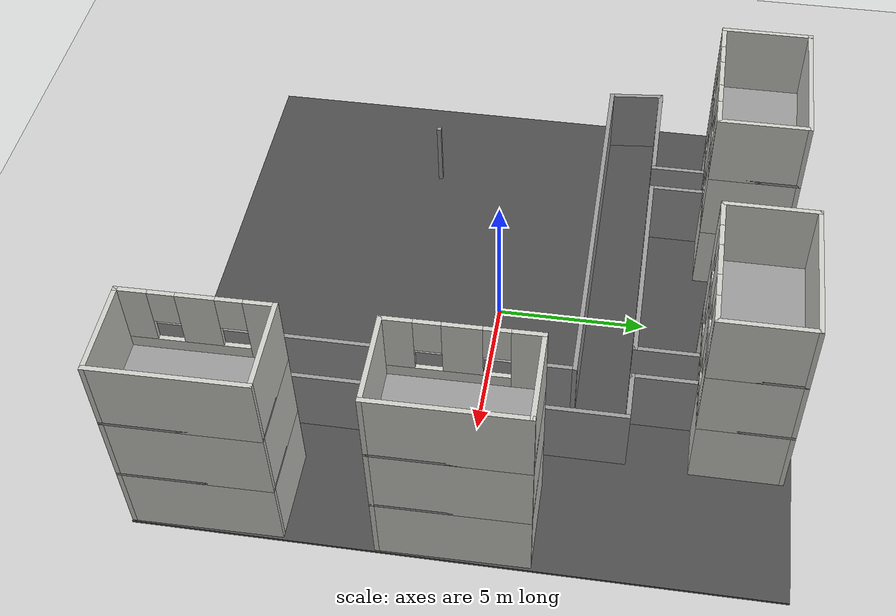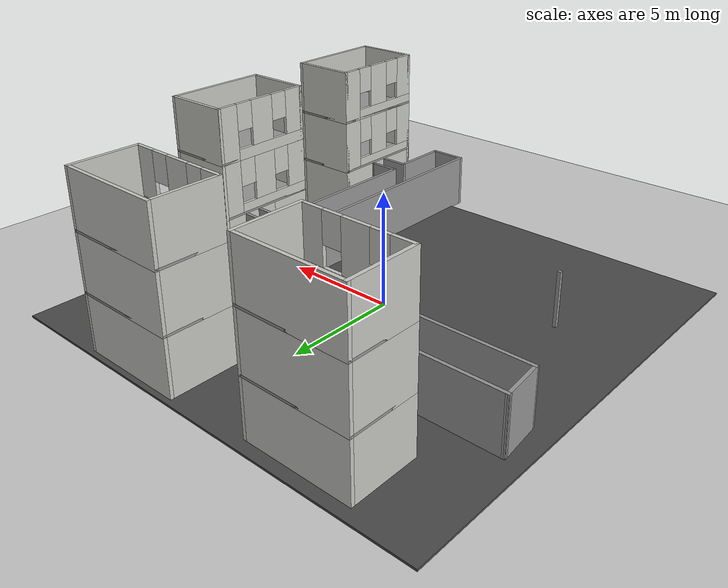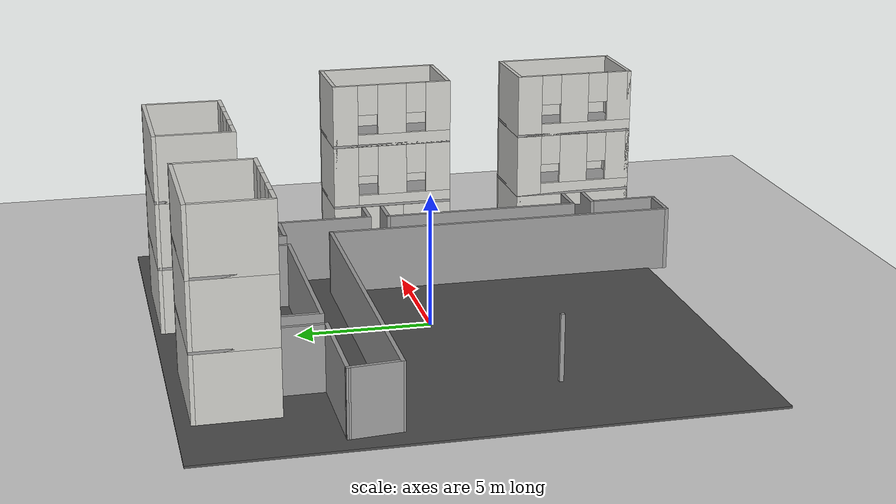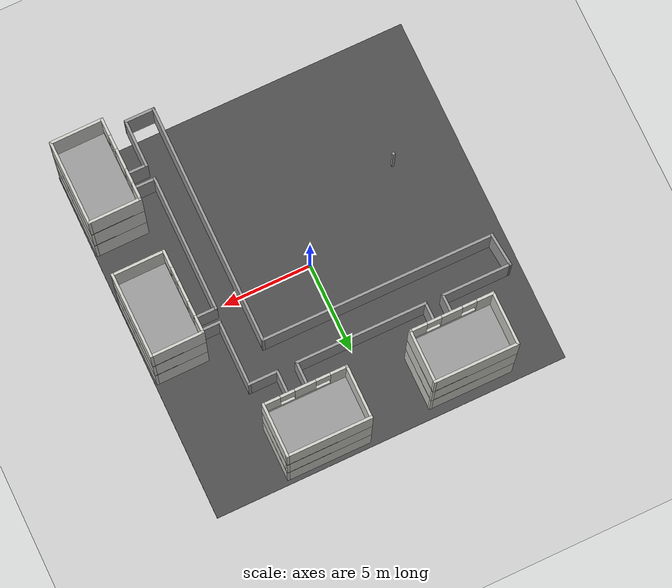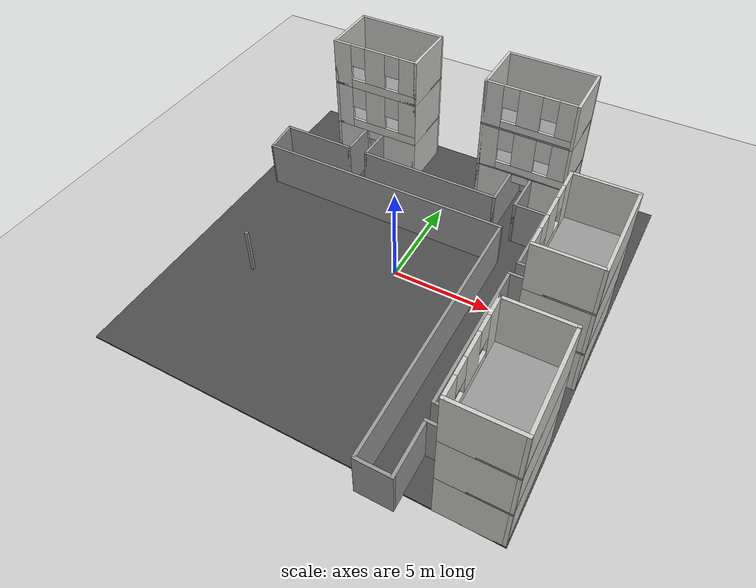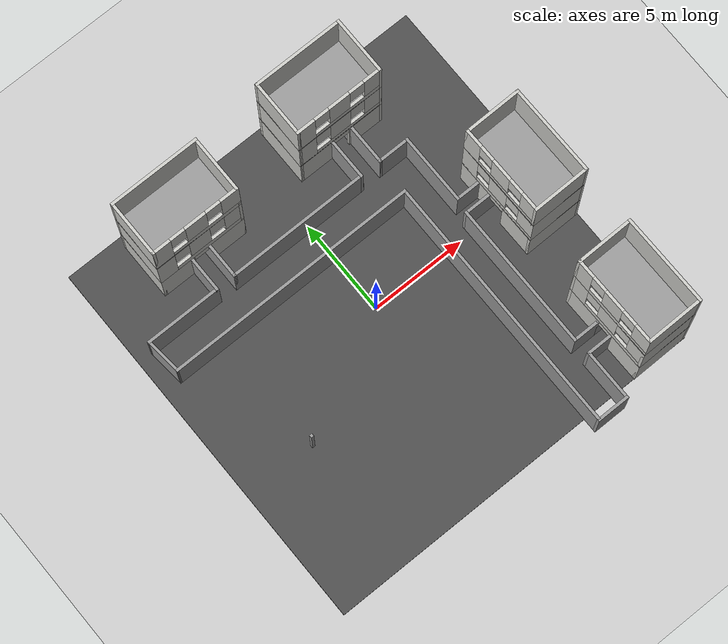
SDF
<sdf version="1.7">
 <world name="default">
  <model name="ground_plane">
   <static>1</static>
   <link name="link">
    <collision name="collision">
     <geometry><plane><normal>0 0 1</normal><size>100 100</size></plane></geometry>
     <surface><friction><ode><mu>100</mu><mu2>50</mu2></ode></friction></surface>
    </collision>
    <visual name="visual">
     <cast_shadows>0</cast_shadows>
     <geometry><plane><normal>0 0 1</normal><size>100 100</size></plane></geometry>
     <material>
      <script><uri>file://media/materials/scripts/gazebo.material</uri><name>Gazebo/Grey</name></script>
     </material>
    </visual>
   </link>
  </model>
  <light name="sun" type="directional">
   <pose>0 0 10 0 -0 0</pose>
   <diffuse>0.8 0.8 0.8 1</diffuse>
   <specular>0.2 0.2 0.2 1</specular>
   <attenuation>
    <range>1000</range>
    <constant>0.9</constant>
    <linear>0.01</linear>
    <quadratic>0.001</quadratic>
   </attenuation>
   <direction>-0.5 0.1 -0.9</direction>
   <spot><inner_angle>0</inner_angle><outer_angle>0</outer_angle><falloff>0</falloff></spot>
  </light>
  <scene><shadows>0</shadows><ambient>0.4 0.4 0.4 1</ambient><background>0.7 0.7 0.7 1</background></scene>
  <physics type="ode">
   <real_time_update_rate>1000</real_time_update_rate>
   <max_step_size>0.001</max_step_size>
   <real_time_factor>1</real_time_factor>
   <ode>
    <solver>
     <type>quick</type>
     <iters>150</iters>
     <precon_iters>0</precon_iters>
     <sor>1.4</sor>
     <use_dynamic_moi_rescaling>1</use_dynamic_moi_rescaling>
    </solver>
    <constraints>
     <cfm>1e-05</cfm>
     <erp>0.2</erp>
     <contact_max_correcting_vel>2000</contact_max_correcting_vel>
     <contact_surface_layer>0.01</contact_surface_layer>
    </constraints>
   </ode>
  </physics>
  <gravity>0 0 -9.8</gravity>
  <magnetic_field>6e-06 2.3e-05 -4.2e-05</magnetic_field>
  <atmosphere type="adiabatic"/>
  <audio><device>default</device></audio>
  <spherical_coordinates>
   <surface_model>EARTH_WGS84</surface_model>
   <latitude_deg>0</latitude_deg>
   <longitude_deg>0</longitude_deg>
   <elevation>0</elevation>
   <heading_deg>0</heading_deg>
  </spherical_coordinates>
  <model name="apt">
   <pose>8.44945 -7.57918 0 0 0 -1.56125</pose>
   <link name="Floor_10">
    <collision name="Floor_10_Collision">
     <geometry><box><size>4.75 3 0.1</size></box></geometry>
     <pose>0 0 0.05 0 -0 0</pose>
    </collision>
    <visual name="Floor_10_Visual">
     <pose>0 0 0.05 0 -0 0</pose>
     <geometry><box><size>4.75 3 0.1</size></box></geometry>
     <material>
      <script><uri>file://media/materials/scripts/gazebo.material</uri><name>Gazebo/Grey</name></script>
      <ambient>1 1 1 1</ambient>
     </material>
     <meta><layer>2</layer></meta>
    </visual>
    <pose>-0 0 5 0 -0 0</pose>
   </link>
   <link name="Floor_9">
    <collision name="Floor_9_Collision">
     <geometry><box><size>4.75 3 0.1</size></box></geometry>
     <pose>0 0 0.05 0 -0 0</pose>
    </collision>
    <visual name="Floor_9_Visual">
     <pose>0 0 0.05 0 -0 0</pose>
     <geometry><box><size>4.75 3 0.1</size></box></geometry>
     <material>
      <script><uri>file://media/materials/scripts/gazebo.material</uri><name>Gazebo/Grey</name></script>
      <ambient>1 1 1 1</ambient>
     </material>
     <meta><layer>1</layer></meta>
    </visual>
    <pose>-0 0 2.5 0 -0 0</pose>
   </link>
   <link name="Wall_1">
    <collision name="Wall_1_Collision">
     <geometry><box><size>3 0.15 2.5</size></box></geometry>
     <pose>0 0 1.25 0 -0 0</pose>
    </collision>
    <visual name="Wall_1_Visual">
     <pose>0 0 1.25 0 -0 0</pose>
     <geometry><box><size>3 0.15 2.5</size></box></geometry>
     <material>
      <script><uri>file://media/materials/scripts/gazebo.material</uri><name>Gazebo/CeilingTiled</name></script>
      <ambient>1 1 1 1</ambient>
     </material>
     <meta><layer>0</layer></meta>
    </visual>
    <pose>-2.3 0 0 0 -0 -1.5708</pose>
   </link>
   <link name="Wall_2">
    <pose>-0 -1.425 0 0 -0 0</pose>
    <visual name="Wall_2_Visual_0">
     <pose>-1.4125 0 1.25 0 -0 0</pose>
     <geometry><box><size>1.925 0.15 2.5</size></box></geometry>
     <material>
      <script><uri>file://media/materials/scripts/gazebo.material</uri><name>Gazebo/CeilingTiled</name></script>
      <ambient>1 1 1 1</ambient>
     </material>
     <meta><layer>0</layer></meta>
    </visual>
    <collision name="Wall_2_Collision_0">
     <geometry><box><size>1.925 0.15 2.5</size></box></geometry>
     <pose>-1.4125 0 1.25 0 -0 0</pose>
    </collision>
    <visual name="Wall_2_Visual_1">
     <pose>1.4125 0 1.25 0 -0 0</pose>
     <geometry><box><size>1.925 0.15 2.5</size></box></geometry>
     <material>
      <script><uri>file://media/materials/scripts/gazebo.material</uri><name>Gazebo/CeilingTiled</name></script>
      <ambient>1 1 1 1</ambient>
     </material>
     <meta><layer>0</layer></meta>
    </visual>
    <collision name="Wall_2_Collision_1">
     <geometry><box><size>1.925 0.15 2.5</size></box></geometry>
     <pose>1.4125 0 1.25 0 -0 0</pose>
    </collision>
    <visual name="Wall_2_Visual_2">
     <pose>0 0 2.25 0 -0 0</pose>
     <geometry><box><size>0.9 0.15 0.5</size></box></geometry>
     <material>
      <script><uri>file://media/materials/scripts/gazebo.material</uri><name>Gazebo/CeilingTiled</name></script>
      <ambient>1 1 1 1</ambient>
     </material>
     <meta><layer>0</layer></meta>
    </visual>
    <collision name="Wall_2_Collision_2">
     <geometry><box><size>0.9 0.15 0.5</size></box></geometry>
     <pose>0 0 2.25 0 -0 0</pose>
    </collision>
   </link>
   <link name="Wall_3">
    <collision name="Wall_3_Collision">
     <geometry><box><size>3 0.15 2.5</size></box></geometry>
     <pose>0 0 1.25 0 -0 0</pose>
    </collision>
    <visual name="Wall_3_Visual">
     <pose>0 0 1.25 0 -0 0</pose>
     <geometry><box><size>3 0.15 2.5</size></box></geometry>
     <material>
      <script><uri>file://media/materials/scripts/gazebo.material</uri><name>Gazebo/CeilingTiled</name></script>
      <ambient>1 1 1 1</ambient>
     </material>
     <meta><layer>0</layer></meta>
    </visual>
    <pose>2.3 0 0 0 -0 1.5708</pose>
   </link>
   <link name="Wall_4">
    <collision name="Wall_4_Collision">
     <geometry><box><size>4.75 0.15 2.5</size></box></geometry>
     <pose>0 0 1.25 0 -0 0</pose>
    </collision>
    <visual name="Wall_4_Visual">
     <pose>0 0 1.25 0 -0 0</pose>
     <geometry><box><size>4.75 0.15 2.5</size></box></geometry>
     <material>
      <script><uri>file://media/materials/scripts/gazebo.material</uri><name>Gazebo/CeilingTiled</name></script>
      <ambient>1 1 1 1</ambient>
     </material>
     <meta><layer>0</layer></meta>
    </visual>
    <pose>-0 1.425 0 0 -0 3.14159</pose>
   </link>
   <link name="Wall_42">
    <collision name="Wall_42_Collision">
     <geometry><box><size>3 0.15 2.5</size></box></geometry>
     <pose>0 0 1.25 0 -0 0</pose>
    </collision>
    <visual name="Wall_42_Visual">
     <pose>0 0 1.25 0 -0 0</pose>
     <geometry><box><size>3 0.15 2.5</size></box></geometry>
     <material>
      <script><uri>file://media/materials/scripts/gazebo.material</uri><name>Gazebo/CeilingTiled</name></script>
      <ambient>1 1 1 1</ambient>
     </material>
     <meta><layer>1</layer></meta>
    </visual>
    <pose>-2.3 0 2.5 0 -0 -1.5708</pose>
   </link>
   <link name="Wall_43">
    <pose>-0 -1.425 2.5 0 -0 0</pose>
    <visual name="Wall_43_Visual_0">
     <pose>-1.87625 0 1.25 0 -0 0</pose>
     <geometry><box><size>0.9975 0.15 2.5</size></box></geometry>
     <material>
      <script><uri>file://media/materials/scripts/gazebo.material</uri><name>Gazebo/CeilingTiled</name></script>
      <ambient>1 1 1 1</ambient>
     </material>
     <meta><layer>1</layer></meta>
    </visual>
    <collision name="Wall_43_Collision_0">
     <geometry><box><size>0.9975 0.15 2.5</size></box></geometry>
     <pose>-1.87625 0 1.25 0 -0 0</pose>
    </collision>
    <visual name="Wall_43_Visual_1">
     <pose>0.49875 0 0.25 0 -0 0</pose>
     <geometry><box><size>3.7525 0.15 0.5</size></box></geometry>
     <material>
      <script><uri>file://media/materials/scripts/gazebo.material</uri><name>Gazebo/CeilingTiled</name></script>
      <ambient>1 1 1 1</ambient>
     </material>
     <meta><layer>1</layer></meta>
    </visual>
    <collision name="Wall_43_Collision_1">
     <geometry><box><size>3.7525 0.15 0.5</size></box></geometry>
     <pose>0.49875 0 0.25 0 -0 0</pose>
    </collision>
    <visual name="Wall_43_Visual_2">
     <pose>0 0 1.5 0 -0 0</pose>
     <geometry><box><size>1.155 0.15 2</size></box></geometry>
     <material>
      <script><uri>file://media/materials/scripts/gazebo.material</uri><name>Gazebo/CeilingTiled</name></script>
      <ambient>1 1 1 1</ambient>
     </material>
     <meta><layer>1</layer></meta>
    </visual>
    <collision name="Wall_43_Collision_2">
     <geometry><box><size>1.155 0.15 2</size></box></geometry>
     <pose>0 0 1.5 0 -0 0</pose>
    </collision>
    <visual name="Wall_43_Visual_3">
     <pose>1.87625 0 1.5 0 -0 0</pose>
     <geometry><box><size>0.9975 0.15 2</size></box></geometry>
     <material>
      <script><uri>file://media/materials/scripts/gazebo.material</uri><name>Gazebo/CeilingTiled</name></script>
      <ambient>1 1 1 1</ambient>
     </material>
     <meta><layer>1</layer></meta>
    </visual>
    <collision name="Wall_43_Collision_3">
     <geometry><box><size>0.9975 0.15 2</size></box></geometry>
     <pose>1.87625 0 1.5 0 -0 0</pose>
    </collision>
    <visual name="Wall_43_Visual_4">
     <pose>-0.9775 0 1.9 0 -0 0</pose>
     <geometry><box><size>0.8 0.15 1.2</size></box></geometry>
     <material>
      <script><uri>file://media/materials/scripts/gazebo.material</uri><name>Gazebo/CeilingTiled</name></script>
      <ambient>1 1 1 1</ambient>
     </material>
     <meta><layer>1</layer></meta>
    </visual>
    <collision name="Wall_43_Collision_4">
     <geometry><box><size>0.8 0.15 1.2</size></box></geometry>
     <pose>-0.9775 0 1.9 0 -0 0</pose>
    </collision>
    <visual name="Wall_43_Visual_5">
     <pose>0.9775 0 1.9 0 -0 0</pose>
     <geometry><box><size>0.8 0.15 1.2</size></box></geometry>
     <material>
      <script><uri>file://media/materials/scripts/gazebo.material</uri><name>Gazebo/CeilingTiled</name></script>
      <ambient>1 1 1 1</ambient>
     </material>
     <meta><layer>1</layer></meta>
    </visual>
    <collision name="Wall_43_Collision_5">
     <geometry><box><size>0.8 0.15 1.2</size></box></geometry>
     <pose>0.9775 0 1.9 0 -0 0</pose>
    </collision>
   </link>
   <link name="Wall_44">
    <collision name="Wall_44_Collision">
     <geometry><box><size>3 0.15 2.5</size></box></geometry>
     <pose>0 0 1.25 0 -0 0</pose>
    </collision>
    <visual name="Wall_44_Visual">
     <pose>0 0 1.25 0 -0 0</pose>
     <geometry><box><size>3 0.15 2.5</size></box></geometry>
     <material>
      <script><uri>file://media/materials/scripts/gazebo.material</uri><name>Gazebo/CeilingTiled</name></script>
      <ambient>1 1 1 1</ambient>
     </material>
     <meta><layer>1</layer></meta>
    </visual>
    <pose>2.3 0 2.5 0 -0 1.5708</pose>
   </link>
   <link name="Wall_45">
    <collision name="Wall_45_Collision">
     <geometry><box><size>4.75 0.15 2.5</size></box></geometry>
     <pose>0 0 1.25 0 -0 0</pose>
    </collision>
    <visual name="Wall_45_Visual">
     <pose>0 0 1.25 0 -0 0</pose>
     <geometry><box><size>4.75 0.15 2.5</size></box></geometry>
     <material>
      <script><uri>file://media/materials/scripts/gazebo.material</uri><name>Gazebo/CeilingTiled</name></script>
      <ambient>1 1 1 1</ambient>
     </material>
     <meta><layer>1</layer></meta>
    </visual>
    <pose>-0 1.425 2.5 0 -0 3.14159</pose>
   </link>
   <link name="Wall_46">
    <collision name="Wall_46_Collision">
     <geometry><box><size>3 0.15 2.5</size></box></geometry>
     <pose>0 0 1.25 0 -0 0</pose>
    </collision>
    <visual name="Wall_46_Visual">
     <pose>0 0 1.25 0 -0 0</pose>
     <geometry><box><size>3 0.15 2.5</size></box></geometry>
     <material>
      <script><uri>file://media/materials/scripts/gazebo.material</uri><name>Gazebo/CeilingTiled</name></script>
      <ambient>1 1 1 1</ambient>
     </material>
     <meta><layer>2</layer></meta>
    </visual>
    <pose>-2.3 0 5 0 -0 -1.5708</pose>
   </link>
   <link name="Wall_47">
    <pose>-0 -1.425 5 0 -0 0</pose>
    <visual name="Wall_47_Visual_0">
     <pose>-1.87625 0 1.25 0 -0 0</pose>
     <geometry><box><size>0.9975 0.15 2.5</size></box></geometry>
     <material>
      <script><uri>file://media/materials/scripts/gazebo.material</uri><name>Gazebo/CeilingTiled</name></script>
      <ambient>1 1 1 1</ambient>
     </material>
     <meta><layer>2</layer></meta>
    </visual>
    <collision name="Wall_47_Collision_0">
     <geometry><box><size>0.9975 0.15 2.5</size></box></geometry>
     <pose>-1.87625 0 1.25 0 -0 0</pose>
    </collision>
    <visual name="Wall_47_Visual_1">
     <pose>0.49875 0 0.25 0 -0 0</pose>
     <geometry><box><size>3.7525 0.15 0.5</size></box></geometry>
     <material>
      <script><uri>file://media/materials/scripts/gazebo.material</uri><name>Gazebo/CeilingTiled</name></script>
      <ambient>1 1 1 1</ambient>
     </material>
     <meta><layer>2</layer></meta>
    </visual>
    <collision name="Wall_47_Collision_1">
     <geometry><box><size>3.7525 0.15 0.5</size></box></geometry>
     <pose>0.49875 0 0.25 0 -0 0</pose>
    </collision>
    <visual name="Wall_47_Visual_2">
     <pose>0 0 1.5 0 -0 0</pose>
     <geometry><box><size>1.155 0.15 2</size></box></geometry>
     <material>
      <script><uri>file://media/materials/scripts/gazebo.material</uri><name>Gazebo/CeilingTiled</name></script>
      <ambient>1 1 1 1</ambient>
     </material>
     <meta><layer>2</layer></meta>
    </visual>
    <collision name="Wall_47_Collision_2">
     <geometry><box><size>1.155 0.15 2</size></box></geometry>
     <pose>0 0 1.5 0 -0 0</pose>
    </collision>
    <visual name="Wall_47_Visual_3">
     <pose>1.87625 0 1.5 0 -0 0</pose>
     <geometry><box><size>0.9975 0.15 2</size></box></geometry>
     <material>
      <script><uri>file://media/materials/scripts/gazebo.material</uri><name>Gazebo/CeilingTiled</name></script>
      <ambient>1 1 1 1</ambient>
     </material>
     <meta><layer>2</layer></meta>
    </visual>
    <collision name="Wall_47_Collision_3">
     <geometry><box><size>0.9975 0.15 2</size></box></geometry>
     <pose>1.87625 0 1.5 0 -0 0</pose>
    </collision>
    <visual name="Wall_47_Visual_4">
     <pose>-0.9775 0 1.9 0 -0 0</pose>
     <geometry><box><size>0.8 0.15 1.2</size></box></geometry>
     <material>
      <script><uri>file://media/materials/scripts/gazebo.material</uri><name>Gazebo/CeilingTiled</name></script>
      <ambient>1 1 1 1</ambient>
     </material>
     <meta><layer>2</layer></meta>
    </visual>
    <collision name="Wall_47_Collision_4">
     <geometry><box><size>0.8 0.15 1.2</size></box></geometry>
     <pose>-0.9775 0 1.9 0 -0 0</pose>
    </collision>
    <visual name="Wall_47_Visual_5">
     <pose>0.9775 0 1.9 0 -0 0</pose>
     <geometry><box><size>0.8 0.15 1.2</size></box></geometry>
     <material>
      <script><uri>file://media/materials/scripts/gazebo.material</uri><name>Gazebo/CeilingTiled</name></script>
      <ambient>1 1 1 1</ambient>
     </material>
     <meta><layer>2</layer></meta>
    </visual>
    <collision name="Wall_47_Collision_5">
     <geometry><box><size>0.8 0.15 1.2</size></box></geometry>
     <pose>0.9775 0 1.9 0 -0 0</pose>
    </collision>
   </link>
   <link name="Wall_48">
    <collision name="Wall_48_Collision">
     <geometry><box><size>3 0.15 2.5</size></box></geometry>
     <pose>0 0 1.25 0 -0 0</pose>
    </collision>
    <visual name="Wall_48_Visual">
     <pose>0 0 1.25 0 -0 0</pose>
     <geometry><box><size>3 0.15 2.5</size></box></geometry>
     <material>
      <script><uri>file://media/materials/scripts/gazebo.material</uri><name>Gazebo/CeilingTiled</name></script>
      <ambient>1 1 1 1</ambient>
     </material>
     <meta><layer>2</layer></meta>
    </visual>
    <pose>2.3 0 5 0 -0 1.5708</pose>
   </link>
   <link name="Wall_49">
    <collision name="Wall_49_Collision">
     <geometry><box><size>4.75 0.15 2.5</size></box></geometry>
     <pose>0 0 1.25 0 -0 0</pose>
    </collision>
    <visual name="Wall_49_Visual">
     <pose>0 0 1.25 0 -0 0</pose>
     <geometry><box><size>4.75 0.15 2.5</size></box></geometry>
     <material>
      <script><uri>file://media/materials/scripts/gazebo.material</uri><name>Gazebo/CeilingTiled</name></script>
      <ambient>1 1 1 1</ambient>
     </material>
     <meta><layer>2</layer></meta>
    </visual>
    <pose>-0 1.425 5 0 -0 3.14159</pose>
   </link>
   <static>1</static>
  </model>
  <model name="asphalt_plane">
   <static>1</static>
   <link name="link">
    <collision name="collision"><geometry><box><size>20 20 0.1</size></box></geometry></collision>
    <visual name="visual">
     <cast_shadows>0</cast_shadows>
     <geometry><box><size>20 20 0.1</size></box></geometry>
     <material>
      <script>
       <uri>model://asphalt_plane/materials/scripts</uri>
       <uri>model://asphalt_plane/materials/textures</uri>
       <name>vrc/asphalt</name>
      </script>
     </material>
    </visual>
   </link>
   <pose>0.008449 0.055519 0 0 -0 0</pose>
  </model>
  <model name="apt_0">
   <pose>3.51198 8.32486 0 0 -0 0</pose>
   <link name="Floor_10">
    <collision name="Floor_10_Collision">
     <geometry><box><size>4.75 3 0.1</size></box></geometry>
     <pose>0 0 0.05 0 -0 0</pose>
    </collision>
    <visual name="Floor_10_Visual">
     <pose>0 0 0.05 0 -0 0</pose>
     <geometry><box><size>4.75 3 0.1</size></box></geometry>
     <material>
      <script><uri>file://media/materials/scripts/gazebo.material</uri><name>Gazebo/Grey</name></script>
      <ambient>1 1 1 1</ambient>
     </material>
     <meta><layer>2</layer></meta>
    </visual>
    <pose>-0 0 5 0 -0 0</pose>
   </link>
   <link name="Floor_9">
    <collision name="Floor_9_Collision">
     <geometry><box><size>4.75 3 0.1</size></box></geometry>
     <pose>0 0 0.05 0 -0 0</pose>
    </collision>
    <visual name="Floor_9_Visual">
     <pose>0 0 0.05 0 -0 0</pose>
     <geometry><box><size>4.75 3 0.1</size></box></geometry>
     <material>
      <script><uri>file://media/materials/scripts/gazebo.material</uri><name>Gazebo/Grey</name></script>
      <ambient>1 1 1 1</ambient>
     </material>
     <meta><layer>1</layer></meta>
    </visual>
    <pose>-0 0 2.5 0 -0 0</pose>
   </link>
   <link name="Wall_1">
    <collision name="Wall_1_Collision">
     <geometry><box><size>3 0.15 2.5</size></box></geometry>
     <pose>0 0 1.25 0 -0 0</pose>
    </collision>
    <visual name="Wall_1_Visual">
     <pose>0 0 1.25 0 -0 0</pose>
     <geometry><box><size>3 0.15 2.5</size></box></geometry>
     <material>
      <script><uri>file://media/materials/scripts/gazebo.material</uri><name>Gazebo/CeilingTiled</name></script>
      <ambient>1 1 1 1</ambient>
     </material>
     <meta><layer>0</layer></meta>
    </visual>
    <pose>-2.3 0 0 0 -0 -1.5708</pose>
   </link>
   <link name="Wall_2">
    <pose>-0 -1.425 0 0 -0 0</pose>
    <visual name="Wall_2_Visual_0">
     <pose>-1.4125 0 1.25 0 -0 0</pose>
     <geometry><box><size>1.925 0.15 2.5</size></box></geometry>
     <material>
      <script><uri>file://media/materials/scripts/gazebo.material</uri><name>Gazebo/CeilingTiled</name></script>
      <ambient>1 1 1 1</ambient>
     </material>
     <meta><layer>0</layer></meta>
    </visual>
    <collision name="Wall_2_Collision_0">
     <geometry><box><size>1.925 0.15 2.5</size></box></geometry>
     <pose>-1.4125 0 1.25 0 -0 0</pose>
    </collision>
    <visual name="Wall_2_Visual_1">
     <pose>1.4125 0 1.25 0 -0 0</pose>
     <geometry><box><size>1.925 0.15 2.5</size></box></geometry>
     <material>
      <script><uri>file://media/materials/scripts/gazebo.material</uri><name>Gazebo/CeilingTiled</name></script>
      <ambient>1 1 1 1</ambient>
     </material>
     <meta><layer>0</layer></meta>
    </visual>
    <collision name="Wall_2_Collision_1">
     <geometry><box><size>1.925 0.15 2.5</size></box></geometry>
     <pose>1.4125 0 1.25 0 -0 0</pose>
    </collision>
    <visual name="Wall_2_Visual_2">
     <pose>0 0 2.25 0 -0 0</pose>
     <geometry><box><size>0.9 0.15 0.5</size></box></geometry>
     <material>
      <script><uri>file://media/materials/scripts/gazebo.material</uri><name>Gazebo/CeilingTiled</name></script>
      <ambient>1 1 1 1</ambient>
     </material>
     <meta><layer>0</layer></meta>
    </visual>
    <collision name="Wall_2_Collision_2">
     <geometry><box><size>0.9 0.15 0.5</size></box></geometry>
     <pose>0 0 2.25 0 -0 0</pose>
    </collision>
   </link>
   <link name="Wall_3">
    <collision name="Wall_3_Collision">
     <geometry><box><size>3 0.15 2.5</size></box></geometry>
     <pose>0 0 1.25 0 -0 0</pose>
    </collision>
    <visual name="Wall_3_Visual">
     <pose>0 0 1.25 0 -0 0</pose>
     <geometry><box><size>3 0.15 2.5</size></box></geometry>
     <material>
      <script><uri>file://media/materials/scripts/gazebo.material</uri><name>Gazebo/CeilingTiled</name></script>
      <ambient>1 1 1 1</ambient>
     </material>
     <meta><layer>0</layer></meta>
    </visual>
    <pose>2.3 0 0 0 -0 1.5708</pose>
   </link>
   <link name="Wall_4">
    <collision name="Wall_4_Collision">
     <geometry><box><size>4.75 0.15 2.5</size></box></geometry>
     <pose>0 0 1.25 0 -0 0</pose>
    </collision>
    <visual name="Wall_4_Visual">
     <pose>0 0 1.25 0 -0 0</pose>
     <geometry><box><size>4.75 0.15 2.5</size></box></geometry>
     <material>
      <script><uri>file://media/materials/scripts/gazebo.material</uri><name>Gazebo/CeilingTiled</name></script>
      <ambient>1 1 1 1</ambient>
     </material>
     <meta><layer>0</layer></meta>
    </visual>
    <pose>-0 1.425 0 0 -0 3.14159</pose>
   </link>
   <link name="Wall_42">
    <collision name="Wall_42_Collision">
     <geometry><box><size>3 0.15 2.5</size></box></geometry>
     <pose>0 0 1.25 0 -0 0</pose>
    </collision>
    <visual name="Wall_42_Visual">
     <pose>0 0 1.25 0 -0 0</pose>
     <geometry><box><size>3 0.15 2.5</size></box></geometry>
     <material>
      <script><uri>file://media/materials/scripts/gazebo.material</uri><name>Gazebo/CeilingTiled</name></script>
      <ambient>1 1 1 1</ambient>
     </material>
     <meta><layer>1</layer></meta>
    </visual>
    <pose>-2.3 0 2.5 0 -0 -1.5708</pose>
   </link>
   <link name="Wall_43">
    <pose>-0 -1.425 2.5 0 -0 0</pose>
    <visual name="Wall_43_Visual_0">
     <pose>-1.87625 0 1.25 0 -0 0</pose>
     <geometry><box><size>0.9975 0.15 2.5</size></box></geometry>
     <material>
      <script><uri>file://media/materials/scripts/gazebo.material</uri><name>Gazebo/CeilingTiled</name></script>
      <ambient>1 1 1 1</ambient>
     </material>
     <meta><layer>1</layer></meta>
    </visual>
    <collision name="Wall_43_Collision_0">
     <geometry><box><size>0.9975 0.15 2.5</size></box></geometry>
     <pose>-1.87625 0 1.25 0 -0 0</pose>
    </collision>
    <visual name="Wall_43_Visual_1">
     <pose>0.49875 0 0.25 0 -0 0</pose>
     <geometry><box><size>3.7525 0.15 0.5</size></box></geometry>
     <material>
      <script><uri>file://media/materials/scripts/gazebo.material</uri><name>Gazebo/CeilingTiled</name></script>
      <ambient>1 1 1 1</ambient>
     </material>
     <meta><layer>1</layer></meta>
    </visual>
    <collision name="Wall_43_Collision_1">
     <geometry><box><size>3.7525 0.15 0.5</size></box></geometry>
     <pose>0.49875 0 0.25 0 -0 0</pose>
    </collision>
    <visual name="Wall_43_Visual_2">
     <pose>0 0 1.5 0 -0 0</pose>
     <geometry><box><size>1.155 0.15 2</size></box></geometry>
     <material>
      <script><uri>file://media/materials/scripts/gazebo.material</uri><name>Gazebo/CeilingTiled</name></script>
      <ambient>1 1 1 1</ambient>
     </material>
     <meta><layer>1</layer></meta>
    </visual>
    <collision name="Wall_43_Collision_2">
     <geometry><box><size>1.155 0.15 2</size></box></geometry>
     <pose>0 0 1.5 0 -0 0</pose>
    </collision>
    <visual name="Wall_43_Visual_3">
     <pose>1.87625 0 1.5 0 -0 0</pose>
     <geometry><box><size>0.9975 0.15 2</size></box></geometry>
     <material>
      <script><uri>file://media/materials/scripts/gazebo.material</uri><name>Gazebo/CeilingTiled</name></script>
      <ambient>1 1 1 1</ambient>
     </material>
     <meta><layer>1</layer></meta>
    </visual>
    <collision name="Wall_43_Collision_3">
     <geometry><box><size>0.9975 0.15 2</size></box></geometry>
     <pose>1.87625 0 1.5 0 -0 0</pose>
    </collision>
    <visual name="Wall_43_Visual_4">
     <pose>-0.9775 0 1.9 0 -0 0</pose>
     <geometry><box><size>0.8 0.15 1.2</size></box></geometry>
     <material>
      <script><uri>file://media/materials/scripts/gazebo.material</uri><name>Gazebo/CeilingTiled</name></script>
      <ambient>1 1 1 1</ambient>
     </material>
     <meta><layer>1</layer></meta>
    </visual>
    <collision name="Wall_43_Collision_4">
     <geometry><box><size>0.8 0.15 1.2</size></box></geometry>
     <pose>-0.9775 0 1.9 0 -0 0</pose>
    </collision>
    <visual name="Wall_43_Visual_5">
     <pose>0.9775 0 1.9 0 -0 0</pose>
     <geometry><box><size>0.8 0.15 1.2</size></box></geometry>
     <material>
      <script><uri>file://media/materials/scripts/gazebo.material</uri><name>Gazebo/CeilingTiled</name></script>
      <ambient>1 1 1 1</ambient>
     </material>
     <meta><layer>1</layer></meta>
    </visual>
    <collision name="Wall_43_Collision_5">
     <geometry><box><size>0.8 0.15 1.2</size></box></geometry>
     <pose>0.9775 0 1.9 0 -0 0</pose>
    </collision>
   </link>
   <link name="Wall_44">
    <collision name="Wall_44_Collision">
     <geometry><box><size>3 0.15 2.5</size></box></geometry>
     <pose>0 0 1.25 0 -0 0</pose>
    </collision>
    <visual name="Wall_44_Visual">
     <pose>0 0 1.25 0 -0 0</pose>
     <geometry><box><size>3 0.15 2.5</size></box></geometry>
     <material>
      <script><uri>file://media/materials/scripts/gazebo.material</uri><name>Gazebo/CeilingTiled</name></script>
      <ambient>1 1 1 1</ambient>
     </material>
     <meta><layer>1</layer></meta>
    </visual>
    <pose>2.3 0 2.5 0 -0 1.5708</pose>
   </link>
   <link name="Wall_45">
    <collision name="Wall_45_Collision">
     <geometry><box><size>4.75 0.15 2.5</size></box></geometry>
     <pose>0 0 1.25 0 -0 0</pose>
    </collision>
    <visual name="Wall_45_Visual">
     <pose>0 0 1.25 0 -0 0</pose>
     <geometry><box><size>4.75 0.15 2.5</size></box></geometry>
     <material>
      <script><uri>file://media/materials/scripts/gazebo.material</uri><name>Gazebo/CeilingTiled</name></script>
      <ambient>1 1 1 1</ambient>
     </material>
     <meta><layer>1</layer></meta>
    </visual>
    <pose>-0 1.425 2.5 0 -0 3.14159</pose>
   </link>
   <link name="Wall_46">
    <collision name="Wall_46_Collision">
     <geometry><box><size>3 0.15 2.5</size></box></geometry>
     <pose>0 0 1.25 0 -0 0</pose>
    </collision>
    <visual name="Wall_46_Visual">
     <pose>0 0 1.25 0 -0 0</pose>
     <geometry><box><size>3 0.15 2.5</size></box></geometry>
     <material>
      <script><uri>file://media/materials/scripts/gazebo.material</uri><name>Gazebo/CeilingTiled</name></script>
      <ambient>1 1 1 1</ambient>
     </material>
     <meta><layer>2</layer></meta>
    </visual>
    <pose>-2.3 0 5 0 -0 -1.5708</pose>
   </link>
   <link name="Wall_47">
    <pose>-0 -1.425 5 0 -0 0</pose>
    <visual name="Wall_47_Visual_0">
     <pose>-1.87625 0 1.25 0 -0 0</pose>
     <geometry><box><size>0.9975 0.15 2.5</size></box></geometry>
     <material>
      <script><uri>file://media/materials/scripts/gazebo.material</uri><name>Gazebo/CeilingTiled</name></script>
      <ambient>1 1 1 1</ambient>
     </material>
     <meta><layer>2</layer></meta>
    </visual>
    <collision name="Wall_47_Collision_0">
     <geometry><box><size>0.9975 0.15 2.5</size></box></geometry>
     <pose>-1.87625 0 1.25 0 -0 0</pose>
    </collision>
    <visual name="Wall_47_Visual_1">
     <pose>0.49875 0 0.25 0 -0 0</pose>
     <geometry><box><size>3.7525 0.15 0.5</size></box></geometry>
     <material>
      <script><uri>file://media/materials/scripts/gazebo.material</uri><name>Gazebo/CeilingTiled</name></script>
      <ambient>1 1 1 1</ambient>
     </material>
     <meta><layer>2</layer></meta>
    </visual>
    <collision name="Wall_47_Collision_1">
     <geometry><box><size>3.7525 0.15 0.5</size></box></geometry>
     <pose>0.49875 0 0.25 0 -0 0</pose>
    </collision>
    <visual name="Wall_47_Visual_2">
     <pose>0 0 1.5 0 -0 0</pose>
     <geometry><box><size>1.155 0.15 2</size></box></geometry>
     <material>
      <script><uri>file://media/materials/scripts/gazebo.material</uri><name>Gazebo/CeilingTiled</name></script>
      <ambient>1 1 1 1</ambient>
     </material>
     <meta><layer>2</layer></meta>
    </visual>
    <collision name="Wall_47_Collision_2">
     <geometry><box><size>1.155 0.15 2</size></box></geometry>
     <pose>0 0 1.5 0 -0 0</pose>
    </collision>
    <visual name="Wall_47_Visual_3">
     <pose>1.87625 0 1.5 0 -0 0</pose>
     <geometry><box><size>0.9975 0.15 2</size></box></geometry>
     <material>
      <script><uri>file://media/materials/scripts/gazebo.material</uri><name>Gazebo/CeilingTiled</name></script>
      <ambient>1 1 1 1</ambient>
     </material>
     <meta><layer>2</layer></meta>
    </visual>
    <collision name="Wall_47_Collision_3">
     <geometry><box><size>0.9975 0.15 2</size></box></geometry>
     <pose>1.87625 0 1.5 0 -0 0</pose>
    </collision>
    <visual name="Wall_47_Visual_4">
     <pose>-0.9775 0 1.9 0 -0 0</pose>
     <geometry><box><size>0.8 0.15 1.2</size></box></geometry>
     <material>
      <script><uri>file://media/materials/scripts/gazebo.material</uri><name>Gazebo/CeilingTiled</name></script>
      <ambient>1 1 1 1</ambient>
     </material>
     <meta><layer>2</layer></meta>
    </visual>
    <collision name="Wall_47_Collision_4">
     <geometry><box><size>0.8 0.15 1.2</size></box></geometry>
     <pose>-0.9775 0 1.9 0 -0 0</pose>
    </collision>
    <visual name="Wall_47_Visual_5">
     <pose>0.9775 0 1.9 0 -0 0</pose>
     <geometry><box><size>0.8 0.15 1.2</size></box></geometry>
     <material>
      <script><uri>file://media/materials/scripts/gazebo.material</uri><name>Gazebo/CeilingTiled</name></script>
      <ambient>1 1 1 1</ambient>
     </material>
     <meta><layer>2</layer></meta>
    </visual>
    <collision name="Wall_47_Collision_5">
     <geometry><box><size>0.8 0.15 1.2</size></box></geometry>
     <pose>0.9775 0 1.9 0 -0 0</pose>
    </collision>
   </link>
   <link name="Wall_48">
    <collision name="Wall_48_Collision">
     <geometry><box><size>3 0.15 2.5</size></box></geometry>
     <pose>0 0 1.25 0 -0 0</pose>
    </collision>
    <visual name="Wall_48_Visual">
     <pose>0 0 1.25 0 -0 0</pose>
     <geometry><box><size>3 0.15 2.5</size></box></geometry>
     <material>
      <script><uri>file://media/materials/scripts/gazebo.material</uri><name>Gazebo/CeilingTiled</name></script>
      <ambient>1 1 1 1</ambient>
     </material>
     <meta><layer>2</layer></meta>
    </visual>
    <pose>2.3 0 5 0 -0 1.5708</pose>
   </link>
   <link name="Wall_49">
    <collision name="Wall_49_Collision">
     <geometry><box><size>4.75 0.15 2.5</size></box></geometry>
     <pose>0 0 1.25 0 -0 0</pose>
    </collision>
    <visual name="Wall_49_Visual">
     <pose>0 0 1.25 0 -0 0</pose>
     <geometry><box><size>4.75 0.15 2.5</size></box></geometry>
     <material>
      <script><uri>file://media/materials/scripts/gazebo.material</uri><name>Gazebo/CeilingTiled</name></script>
      <ambient>1 1 1 1</ambient>
     </material>
     <meta><layer>2</layer></meta>
    </visual>
    <pose>-0 1.425 5 0 -0 3.14159</pose>
   </link>
   <static>1</static>
  </model>
  <model name="apt_1">
   <pose>-4.73085 8.05219 0 0 -0 0</pose>
   <link name="Floor_10">
    <collision name="Floor_10_Collision">
     <geometry><box><size>4.75 3 0.1</size></box></geometry>
     <pose>0 0 0.05 0 -0 0</pose>
    </collision>
    <visual name="Floor_10_Visual">
     <pose>0 0 0.05 0 -0 0</pose>
     <geometry><box><size>4.75 3 0.1</size></box></geometry>
     <material>
      <script><uri>file://media/materials/scripts/gazebo.material</uri><name>Gazebo/Grey</name></script>
      <ambient>1 1 1 1</ambient>
     </material>
     <meta><layer>2</layer></meta>
    </visual>
    <pose>-0 0 5 0 -0 0</pose>
   </link>
   <link name="Floor_9">
    <collision name="Floor_9_Collision">
     <geometry><box><size>4.75 3 0.1</size></box></geometry>
     <pose>0 0 0.05 0 -0 0</pose>
    </collision>
    <visual name="Floor_9_Visual">
     <pose>0 0 0.05 0 -0 0</pose>
     <geometry><box><size>4.75 3 0.1</size></box></geometry>
     <material>
      <script><uri>file://media/materials/scripts/gazebo.material</uri><name>Gazebo/Grey</name></script>
      <ambient>1 1 1 1</ambient>
     </material>
     <meta><layer>1</layer></meta>
    </visual>
    <pose>-0 0 2.5 0 -0 0</pose>
   </link>
   <link name="Wall_1">
    <collision name="Wall_1_Collision">
     <geometry><box><size>3 0.15 2.5</size></box></geometry>
     <pose>0 0 1.25 0 -0 0</pose>
    </collision>
    <visual name="Wall_1_Visual">
     <pose>0 0 1.25 0 -0 0</pose>
     <geometry><box><size>3 0.15 2.5</size></box></geometry>
     <material>
      <script><uri>file://media/materials/scripts/gazebo.material</uri><name>Gazebo/CeilingTiled</name></script>
      <ambient>1 1 1 1</ambient>
     </material>
     <meta><layer>0</layer></meta>
    </visual>
    <pose>-2.3 0 0 0 -0 -1.5708</pose>
   </link>
   <link name="Wall_2">
    <pose>-0 -1.425 0 0 -0 0</pose>
    <visual name="Wall_2_Visual_0">
     <pose>-1.4125 0 1.25 0 -0 0</pose>
     <geometry><box><size>1.925 0.15 2.5</size></box></geometry>
     <material>
      <script><uri>file://media/materials/scripts/gazebo.material</uri><name>Gazebo/CeilingTiled</name></script>
      <ambient>1 1 1 1</ambient>
     </material>
     <meta><layer>0</layer></meta>
    </visual>
    <collision name="Wall_2_Collision_0">
     <geometry><box><size>1.925 0.15 2.5</size></box></geometry>
     <pose>-1.4125 0 1.25 0 -0 0</pose>
    </collision>
    <visual name="Wall_2_Visual_1">
     <pose>1.4125 0 1.25 0 -0 0</pose>
     <geometry><box><size>1.925 0.15 2.5</size></box></geometry>
     <material>
      <script><uri>file://media/materials/scripts/gazebo.material</uri><name>Gazebo/CeilingTiled</name></script>
      <ambient>1 1 1 1</ambient>
     </material>
     <meta><layer>0</layer></meta>
    </visual>
    <collision name="Wall_2_Collision_1">
     <geometry><box><size>1.925 0.15 2.5</size></box></geometry>
     <pose>1.4125 0 1.25 0 -0 0</pose>
    </collision>
    <visual name="Wall_2_Visual_2">
     <pose>0 0 2.25 0 -0 0</pose>
     <geometry><box><size>0.9 0.15 0.5</size></box></geometry>
     <material>
      <script><uri>file://media/materials/scripts/gazebo.material</uri><name>Gazebo/CeilingTiled</name></script>
      <ambient>1 1 1 1</ambient>
     </material>
     <meta><layer>0</layer></meta>
    </visual>
    <collision name="Wall_2_Collision_2">
     <geometry><box><size>0.9 0.15 0.5</size></box></geometry>
     <pose>0 0 2.25 0 -0 0</pose>
    </collision>
   </link>
   <link name="Wall_3">
    <collision name="Wall_3_Collision">
     <geometry><box><size>3 0.15 2.5</size></box></geometry>
     <pose>0 0 1.25 0 -0 0</pose>
    </collision>
    <visual name="Wall_3_Visual">
     <pose>0 0 1.25 0 -0 0</pose>
     <geometry><box><size>3 0.15 2.5</size></box></geometry>
     <material>
      <script><uri>file://media/materials/scripts/gazebo.material</uri><name>Gazebo/CeilingTiled</name></script>
      <ambient>1 1 1 1</ambient>
     </material>
     <meta><layer>0</layer></meta>
    </visual>
    <pose>2.3 0 0 0 -0 1.5708</pose>
   </link>
   <link name="Wall_4">
    <collision name="Wall_4_Collision">
     <geometry><box><size>4.75 0.15 2.5</size></box></geometry>
     <pose>0 0 1.25 0 -0 0</pose>
    </collision>
    <visual name="Wall_4_Visual">
     <pose>0 0 1.25 0 -0 0</pose>
     <geometry><box><size>4.75 0.15 2.5</size></box></geometry>
     <material>
      <script><uri>file://media/materials/scripts/gazebo.material</uri><name>Gazebo/CeilingTiled</name></script>
      <ambient>1 1 1 1</ambient>
     </material>
     <meta><layer>0</layer></meta>
    </visual>
    <pose>-0 1.425 0 0 -0 3.14159</pose>
   </link>
   <link name="Wall_42">
    <collision name="Wall_42_Collision">
     <geometry><box><size>3 0.15 2.5</size></box></geometry>
     <pose>0 0 1.25 0 -0 0</pose>
    </collision>
    <visual name="Wall_42_Visual">
     <pose>0 0 1.25 0 -0 0</pose>
     <geometry><box><size>3 0.15 2.5</size></box></geometry>
     <material>
      <script><uri>file://media/materials/scripts/gazebo.material</uri><name>Gazebo/CeilingTiled</name></script>
      <ambient>1 1 1 1</ambient>
     </material>
     <meta><layer>1</layer></meta>
    </visual>
    <pose>-2.3 0 2.5 0 -0 -1.5708</pose>
   </link>
   <link name="Wall_43">
    <pose>-0 -1.425 2.5 0 -0 0</pose>
    <visual name="Wall_43_Visual_0">
     <pose>-1.87625 0 1.25 0 -0 0</pose>
     <geometry><box><size>0.9975 0.15 2.5</size></box></geometry>
     <material>
      <script><uri>file://media/materials/scripts/gazebo.material</uri><name>Gazebo/CeilingTiled</name></script>
      <ambient>1 1 1 1</ambient>
     </material>
     <meta><layer>1</layer></meta>
    </visual>
    <collision name="Wall_43_Collision_0">
     <geometry><box><size>0.9975 0.15 2.5</size></box></geometry>
     <pose>-1.87625 0 1.25 0 -0 0</pose>
    </collision>
    <visual name="Wall_43_Visual_1">
     <pose>0.49875 0 0.25 0 -0 0</pose>
     <geometry><box><size>3.7525 0.15 0.5</size></box></geometry>
     <material>
      <script><uri>file://media/materials/scripts/gazebo.material</uri><name>Gazebo/CeilingTiled</name></script>
      <ambient>1 1 1 1</ambient>
     </material>
     <meta><layer>1</layer></meta>
    </visual>
    <collision name="Wall_43_Collision_1">
     <geometry><box><size>3.7525 0.15 0.5</size></box></geometry>
     <pose>0.49875 0 0.25 0 -0 0</pose>
    </collision>
    <visual name="Wall_43_Visual_2">
     <pose>0 0 1.5 0 -0 0</pose>
     <geometry><box><size>1.155 0.15 2</size></box></geometry>
     <material>
      <script><uri>file://media/materials/scripts/gazebo.material</uri><name>Gazebo/CeilingTiled</name></script>
      <ambient>1 1 1 1</ambient>
     </material>
     <meta><layer>1</layer></meta>
    </visual>
    <collision name="Wall_43_Collision_2">
     <geometry><box><size>1.155 0.15 2</size></box></geometry>
     <pose>0 0 1.5 0 -0 0</pose>
    </collision>
    <visual name="Wall_43_Visual_3">
     <pose>1.87625 0 1.5 0 -0 0</pose>
     <geometry><box><size>0.9975 0.15 2</size></box></geometry>
     <material>
      <script><uri>file://media/materials/scripts/gazebo.material</uri><name>Gazebo/CeilingTiled</name></script>
      <ambient>1 1 1 1</ambient>
     </material>
     <meta><layer>1</layer></meta>
    </visual>
    <collision name="Wall_43_Collision_3">
     <geometry><box><size>0.9975 0.15 2</size></box></geometry>
     <pose>1.87625 0 1.5 0 -0 0</pose>
    </collision>
    <visual name="Wall_43_Visual_4">
     <pose>-0.9775 0 1.9 0 -0 0</pose>
     <geometry><box><size>0.8 0.15 1.2</size></box></geometry>
     <material>
      <script><uri>file://media/materials/scripts/gazebo.material</uri><name>Gazebo/CeilingTiled</name></script>
      <ambient>1 1 1 1</ambient>
     </material>
     <meta><layer>1</layer></meta>
    </visual>
    <collision name="Wall_43_Collision_4">
     <geometry><box><size>0.8 0.15 1.2</size></box></geometry>
     <pose>-0.9775 0 1.9 0 -0 0</pose>
    </collision>
    <visual name="Wall_43_Visual_5">
     <pose>0.9775 0 1.9 0 -0 0</pose>
     <geometry><box><size>0.8 0.15 1.2</size></box></geometry>
     <material>
      <script><uri>file://media/materials/scripts/gazebo.material</uri><name>Gazebo/CeilingTiled</name></script>
      <ambient>1 1 1 1</ambient>
     </material>
     <meta><layer>1</layer></meta>
    </visual>
    <collision name="Wall_43_Collision_5">
     <geometry><box><size>0.8 0.15 1.2</size></box></geometry>
     <pose>0.9775 0 1.9 0 -0 0</pose>
    </collision>
   </link>
   <link name="Wall_44">
    <collision name="Wall_44_Collision">
     <geometry><box><size>3 0.15 2.5</size></box></geometry>
     <pose>0 0 1.25 0 -0 0</pose>
    </collision>
    <visual name="Wall_44_Visual">
     <pose>0 0 1.25 0 -0 0</pose>
     <geometry><box><size>3 0.15 2.5</size></box></geometry>
     <material>
      <script><uri>file://media/materials/scripts/gazebo.material</uri><name>Gazebo/CeilingTiled</name></script>
      <ambient>1 1 1 1</ambient>
     </material>
     <meta><layer>1</layer></meta>
    </visual>
    <pose>2.3 0 2.5 0 -0 1.5708</pose>
   </link>
   <link name="Wall_45">
    <collision name="Wall_45_Collision">
     <geometry><box><size>4.75 0.15 2.5</size></box></geometry>
     <pose>0 0 1.25 0 -0 0</pose>
    </collision>
    <visual name="Wall_45_Visual">
     <pose>0 0 1.25 0 -0 0</pose>
     <geometry><box><size>4.75 0.15 2.5</size></box></geometry>
     <material>
      <script><uri>file://media/materials/scripts/gazebo.material</uri><name>Gazebo/CeilingTiled</name></script>
      <ambient>1 1 1 1</ambient>
     </material>
     <meta><layer>1</layer></meta>
    </visual>
    <pose>-0 1.425 2.5 0 -0 3.14159</pose>
   </link>
   <link name="Wall_46">
    <collision name="Wall_46_Collision">
     <geometry><box><size>3 0.15 2.5</size></box></geometry>
     <pose>0 0 1.25 0 -0 0</pose>
    </collision>
    <visual name="Wall_46_Visual">
     <pose>0 0 1.25 0 -0 0</pose>
     <geometry><box><size>3 0.15 2.5</size></box></geometry>
     <material>
      <script><uri>file://media/materials/scripts/gazebo.material</uri><name>Gazebo/CeilingTiled</name></script>
      <ambient>1 1 1 1</ambient>
     </material>
     <meta><layer>2</layer></meta>
    </visual>
    <pose>-2.3 0 5 0 -0 -1.5708</pose>
   </link>
   <link name="Wall_47">
    <pose>-0 -1.425 5 0 -0 0</pose>
    <visual name="Wall_47_Visual_0">
     <pose>-1.87625 0 1.25 0 -0 0</pose>
     <geometry><box><size>0.9975 0.15 2.5</size></box></geometry>
     <material>
      <script><uri>file://media/materials/scripts/gazebo.material</uri><name>Gazebo/CeilingTiled</name></script>
      <ambient>1 1 1 1</ambient>
     </material>
     <meta><layer>2</layer></meta>
    </visual>
    <collision name="Wall_47_Collision_0">
     <geometry><box><size>0.9975 0.15 2.5</size></box></geometry>
     <pose>-1.87625 0 1.25 0 -0 0</pose>
    </collision>
    <visual name="Wall_47_Visual_1">
     <pose>0.49875 0 0.25 0 -0 0</pose>
     <geometry><box><size>3.7525 0.15 0.5</size></box></geometry>
     <material>
      <script><uri>file://media/materials/scripts/gazebo.material</uri><name>Gazebo/CeilingTiled</name></script>
      <ambient>1 1 1 1</ambient>
     </material>
     <meta><layer>2</layer></meta>
    </visual>
    <collision name="Wall_47_Collision_1">
     <geometry><box><size>3.7525 0.15 0.5</size></box></geometry>
     <pose>0.49875 0 0.25 0 -0 0</pose>
    </collision>
    <visual name="Wall_47_Visual_2">
     <pose>0 0 1.5 0 -0 0</pose>
     <geometry><box><size>1.155 0.15 2</size></box></geometry>
     <material>
      <script><uri>file://media/materials/scripts/gazebo.material</uri><name>Gazebo/CeilingTiled</name></script>
      <ambient>1 1 1 1</ambient>
     </material>
     <meta><layer>2</layer></meta>
    </visual>
    <collision name="Wall_47_Collision_2">
     <geometry><box><size>1.155 0.15 2</size></box></geometry>
     <pose>0 0 1.5 0 -0 0</pose>
    </collision>
    <visual name="Wall_47_Visual_3">
     <pose>1.87625 0 1.5 0 -0 0</pose>
     <geometry><box><size>0.9975 0.15 2</size></box></geometry>
     <material>
      <script><uri>file://media/materials/scripts/gazebo.material</uri><name>Gazebo/CeilingTiled</name></script>
      <ambient>1 1 1 1</ambient>
     </material>
     <meta><layer>2</layer></meta>
    </visual>
    <collision name="Wall_47_Collision_3">
     <geometry><box><size>0.9975 0.15 2</size></box></geometry>
     <pose>1.87625 0 1.5 0 -0 0</pose>
    </collision>
    <visual name="Wall_47_Visual_4">
     <pose>-0.9775 0 1.9 0 -0 0</pose>
     <geometry><box><size>0.8 0.15 1.2</size></box></geometry>
     <material>
      <script><uri>file://media/materials/scripts/gazebo.material</uri><name>Gazebo/CeilingTiled</name></script>
      <ambient>1 1 1 1</ambient>
     </material>
     <meta><layer>2</layer></meta>
    </visual>
    <collision name="Wall_47_Collision_4">
     <geometry><box><size>0.8 0.15 1.2</size></box></geometry>
     <pose>-0.9775 0 1.9 0 -0 0</pose>
    </collision>
    <visual name="Wall_47_Visual_5">
     <pose>0.9775 0 1.9 0 -0 0</pose>
     <geometry><box><size>0.8 0.15 1.2</size></box></geometry>
     <material>
      <script><uri>file://media/materials/scripts/gazebo.material</uri><name>Gazebo/CeilingTiled</name></script>
      <ambient>1 1 1 1</ambient>
     </material>
     <meta><layer>2</layer></meta>
    </visual>
    <collision name="Wall_47_Collision_5">
     <geometry><box><size>0.8 0.15 1.2</size></box></geometry>
     <pose>0.9775 0 1.9 0 -0 0</pose>
    </collision>
   </link>
   <link name="Wall_48">
    <collision name="Wall_48_Collision">
     <geometry><box><size>3 0.15 2.5</size></box></geometry>
     <pose>0 0 1.25 0 -0 0</pose>
    </collision>
    <visual name="Wall_48_Visual">
     <pose>0 0 1.25 0 -0 0</pose>
     <geometry><box><size>3 0.15 2.5</size></box></geometry>
     <material>
      <script><uri>file://media/materials/scripts/gazebo.material</uri><name>Gazebo/CeilingTiled</name></script>
      <ambient>1 1 1 1</ambient>
     </material>
     <meta><layer>2</layer></meta>
    </visual>
    <pose>2.3 0 5 0 -0 1.5708</pose>
   </link>
   <link name="Wall_49">
    <collision name="Wall_49_Collision">
     <geometry><box><size>4.75 0.15 2.5</size></box></geometry>
     <pose>0 0 1.25 0 -0 0</pose>
    </collision>
    <visual name="Wall_49_Visual">
     <pose>0 0 1.25 0 -0 0</pose>
     <geometry><box><size>4.75 0.15 2.5</size></box></geometry>
     <material>
      <script><uri>file://media/materials/scripts/gazebo.material</uri><name>Gazebo/CeilingTiled</name></script>
      <ambient>1 1 1 1</ambient>
     </material>
     <meta><layer>2</layer></meta>
    </visual>
    <pose>-0 1.425 5 0 -0 3.14159</pose>
   </link>
   <static>1</static>
  </model>
  <model name="apt_clone">
   <pose>8.44557 -0.016768 0 0 0 -1.56125</pose>
   <link name="Floor_10">
    <collision name="Floor_10_Collision">
     <geometry><box><size>4.75 3 0.1</size></box></geometry>
     <pose>0 0 0.05 0 -0 0</pose>
    </collision>
    <visual name="Floor_10_Visual">
     <pose>0 0 0.05 0 -0 0</pose>
     <geometry><box><size>4.75 3 0.1</size></box></geometry>
     <material>
      <script><uri>file://media/materials/scripts/gazebo.material</uri><name>Gazebo/Grey</name></script>
      <ambient>1 1 1 1</ambient>
     </material>
     <meta><layer>2</layer></meta>
    </visual>
    <pose>-0 0 5 0 -0 0</pose>
   </link>
   <link name="Floor_9">
    <collision name="Floor_9_Collision">
     <geometry><box><size>4.75 3 0.1</size></box></geometry>
     <pose>0 0 0.05 0 -0 0</pose>
    </collision>
    <visual name="Floor_9_Visual">
     <pose>0 0 0.05 0 -0 0</pose>
     <geometry><box><size>4.75 3 0.1</size></box></geometry>
     <material>
      <script><uri>file://media/materials/scripts/gazebo.material</uri><name>Gazebo/Grey</name></script>
      <ambient>1 1 1 1</ambient>
     </material>
     <meta><layer>1</layer></meta>
    </visual>
    <pose>-0 0 2.5 0 -0 0</pose>
   </link>
   <link name="Wall_1">
    <collision name="Wall_1_Collision">
     <geometry><box><size>3 0.15 2.5</size></box></geometry>
     <pose>0 0 1.25 0 -0 0</pose>
    </collision>
    <visual name="Wall_1_Visual">
     <pose>0 0 1.25 0 -0 0</pose>
     <geometry><box><size>3 0.15 2.5</size></box></geometry>
     <material>
      <script><uri>file://media/materials/scripts/gazebo.material</uri><name>Gazebo/CeilingTiled</name></script>
      <ambient>1 1 1 1</ambient>
     </material>
     <meta><layer>0</layer></meta>
    </visual>
    <pose>-2.3 0 0 0 -0 -1.5708</pose>
   </link>
   <link name="Wall_2">
    <pose>-0 -1.425 0 0 -0 0</pose>
    <visual name="Wall_2_Visual_0">
     <pose>-1.4125 0 1.25 0 -0 0</pose>
     <geometry><box><size>1.925 0.15 2.5</size></box></geometry>
     <material>
      <script><uri>file://media/materials/scripts/gazebo.material</uri><name>Gazebo/CeilingTiled</name></script>
      <ambient>1 1 1 1</ambient>
     </material>
     <meta><layer>0</layer></meta>
    </visual>
    <collision name="Wall_2_Collision_0">
     <geometry><box><size>1.925 0.15 2.5</size></box></geometry>
     <pose>-1.4125 0 1.25 0 -0 0</pose>
    </collision>
    <visual name="Wall_2_Visual_1">
     <pose>1.4125 0 1.25 0 -0 0</pose>
     <geometry><box><size>1.925 0.15 2.5</size></box></geometry>
     <material>
      <script><uri>file://media/materials/scripts/gazebo.material</uri><name>Gazebo/CeilingTiled</name></script>
      <ambient>1 1 1 1</ambient>
     </material>
     <meta><layer>0</layer></meta>
    </visual>
    <collision name="Wall_2_Collision_1">
     <geometry><box><size>1.925 0.15 2.5</size></box></geometry>
     <pose>1.4125 0 1.25 0 -0 0</pose>
    </collision>
    <visual name="Wall_2_Visual_2">
     <pose>0 0 2.25 0 -0 0</pose>
     <geometry><box><size>0.9 0.15 0.5</size></box></geometry>
     <material>
      <script><uri>file://media/materials/scripts/gazebo.material</uri><name>Gazebo/CeilingTiled</name></script>
      <ambient>1 1 1 1</ambient>
     </material>
     <meta><layer>0</layer></meta>
    </visual>
    <collision name="Wall_2_Collision_2">
     <geometry><box><size>0.9 0.15 0.5</size></box></geometry>
     <pose>0 0 2.25 0 -0 0</pose>
    </collision>
   </link>
   <link name="Wall_3">
    <collision name="Wall_3_Collision">
     <geometry><box><size>3 0.15 2.5</size></box></geometry>
     <pose>0 0 1.25 0 -0 0</pose>
    </collision>
    <visual name="Wall_3_Visual">
     <pose>0 0 1.25 0 -0 0</pose>
     <geometry><box><size>3 0.15 2.5</size></box></geometry>
     <material>
      <script><uri>file://media/materials/scripts/gazebo.material</uri><name>Gazebo/CeilingTiled</name></script>
      <ambient>1 1 1 1</ambient>
     </material>
     <meta><layer>0</layer></meta>
    </visual>
    <pose>2.3 0 0 0 -0 1.5708</pose>
   </link>
   <link name="Wall_4">
    <collision name="Wall_4_Collision">
     <geometry><box><size>4.75 0.15 2.5</size></box></geometry>
     <pose>0 0 1.25 0 -0 0</pose>
    </collision>
    <visual name="Wall_4_Visual">
     <pose>0 0 1.25 0 -0 0</pose>
     <geometry><box><size>4.75 0.15 2.5</size></box></geometry>
     <material>
      <script><uri>file://media/materials/scripts/gazebo.material</uri><name>Gazebo/CeilingTiled</name></script>
      <ambient>1 1 1 1</ambient>
     </material>
     <meta><layer>0</layer></meta>
    </visual>
    <pose>-0 1.425 0 0 -0 3.14159</pose>
   </link>
   <link name="Wall_42">
    <collision name="Wall_42_Collision">
     <geometry><box><size>3 0.15 2.5</size></box></geometry>
     <pose>0 0 1.25 0 -0 0</pose>
    </collision>
    <visual name="Wall_42_Visual">
     <pose>0 0 1.25 0 -0 0</pose>
     <geometry><box><size>3 0.15 2.5</size></box></geometry>
     <material>
      <script><uri>file://media/materials/scripts/gazebo.material</uri><name>Gazebo/CeilingTiled</name></script>
      <ambient>1 1 1 1</ambient>
     </material>
     <meta><layer>1</layer></meta>
    </visual>
    <pose>-2.3 0 2.5 0 -0 -1.5708</pose>
   </link>
   <link name="Wall_43">
    <pose>-0 -1.425 2.5 0 -0 0</pose>
    <visual name="Wall_43_Visual_0">
     <pose>-1.87625 0 1.25 0 -0 0</pose>
     <geometry><box><size>0.9975 0.15 2.5</size></box></geometry>
     <material>
      <script><uri>file://media/materials/scripts/gazebo.material</uri><name>Gazebo/CeilingTiled</name></script>
      <ambient>1 1 1 1</ambient>
     </material>
     <meta><layer>1</layer></meta>
    </visual>
    <collision name="Wall_43_Collision_0">
     <geometry><box><size>0.9975 0.15 2.5</size></box></geometry>
     <pose>-1.87625 0 1.25 0 -0 0</pose>
    </collision>
    <visual name="Wall_43_Visual_1">
     <pose>0.49875 0 0.25 0 -0 0</pose>
     <geometry><box><size>3.7525 0.15 0.5</size></box></geometry>
     <material>
      <script><uri>file://media/materials/scripts/gazebo.material</uri><name>Gazebo/CeilingTiled</name></script>
      <ambient>1 1 1 1</ambient>
     </material>
     <meta><layer>1</layer></meta>
    </visual>
    <collision name="Wall_43_Collision_1">
     <geometry><box><size>3.7525 0.15 0.5</size></box></geometry>
     <pose>0.49875 0 0.25 0 -0 0</pose>
    </collision>
    <visual name="Wall_43_Visual_2">
     <pose>0 0 1.5 0 -0 0</pose>
     <geometry><box><size>1.155 0.15 2</size></box></geometry>
     <material>
      <script><uri>file://media/materials/scripts/gazebo.material</uri><name>Gazebo/CeilingTiled</name></script>
      <ambient>1 1 1 1</ambient>
     </material>
     <meta><layer>1</layer></meta>
    </visual>
    <collision name="Wall_43_Collision_2">
     <geometry><box><size>1.155 0.15 2</size></box></geometry>
     <pose>0 0 1.5 0 -0 0</pose>
    </collision>
    <visual name="Wall_43_Visual_3">
     <pose>1.87625 0 1.5 0 -0 0</pose>
     <geometry><box><size>0.9975 0.15 2</size></box></geometry>
     <material>
      <script><uri>file://media/materials/scripts/gazebo.material</uri><name>Gazebo/CeilingTiled</name></script>
      <ambient>1 1 1 1</ambient>
     </material>
     <meta><layer>1</layer></meta>
    </visual>
    <collision name="Wall_43_Collision_3">
     <geometry><box><size>0.9975 0.15 2</size></box></geometry>
     <pose>1.87625 0 1.5 0 -0 0</pose>
    </collision>
    <visual name="Wall_43_Visual_4">
     <pose>-0.9775 0 1.9 0 -0 0</pose>
     <geometry><box><size>0.8 0.15 1.2</size></box></geometry>
     <material>
      <script><uri>file://media/materials/scripts/gazebo.material</uri><name>Gazebo/CeilingTiled</name></script>
      <ambient>1 1 1 1</ambient>
     </material>
     <meta><layer>1</layer></meta>
    </visual>
    <collision name="Wall_43_Collision_4">
     <geometry><box><size>0.8 0.15 1.2</size></box></geometry>
     <pose>-0.9775 0 1.9 0 -0 0</pose>
    </collision>
    <visual name="Wall_43_Visual_5">
     <pose>0.9775 0 1.9 0 -0 0</pose>
     <geometry><box><size>0.8 0.15 1.2</size></box></geometry>
     <material>
      <script><uri>file://media/materials/scripts/gazebo.material</uri><name>Gazebo/CeilingTiled</name></script>
      <ambient>1 1 1 1</ambient>
     </material>
     <meta><layer>1</layer></meta>
    </visual>
    <collision name="Wall_43_Collision_5">
     <geometry><box><size>0.8 0.15 1.2</size></box></geometry>
     <pose>0.9775 0 1.9 0 -0 0</pose>
    </collision>
   </link>
   <link name="Wall_44">
    <collision name="Wall_44_Collision">
     <geometry><box><size>3 0.15 2.5</size></box></geometry>
     <pose>0 0 1.25 0 -0 0</pose>
    </collision>
    <visual name="Wall_44_Visual">
     <pose>0 0 1.25 0 -0 0</pose>
     <geometry><box><size>3 0.15 2.5</size></box></geometry>
     <material>
      <script><uri>file://media/materials/scripts/gazebo.material</uri><name>Gazebo/CeilingTiled</name></script>
      <ambient>1 1 1 1</ambient>
     </material>
     <meta><layer>1</layer></meta>
    </visual>
    <pose>2.3 0 2.5 0 -0 1.5708</pose>
   </link>
   <link name="Wall_45">
    <collision name="Wall_45_Collision">
     <geometry><box><size>4.75 0.15 2.5</size></box></geometry>
     <pose>0 0 1.25 0 -0 0</pose>
    </collision>
    <visual name="Wall_45_Visual">
     <pose>0 0 1.25 0 -0 0</pose>
     <geometry><box><size>4.75 0.15 2.5</size></box></geometry>
     <material>
      <script><uri>file://media/materials/scripts/gazebo.material</uri><name>Gazebo/CeilingTiled</name></script>
      <ambient>1 1 1 1</ambient>
     </material>
     <meta><layer>1</layer></meta>
    </visual>
    <pose>-0 1.425 2.5 0 -0 3.14159</pose>
   </link>
   <link name="Wall_46">
    <collision name="Wall_46_Collision">
     <geometry><box><size>3 0.15 2.5</size></box></geometry>
     <pose>0 0 1.25 0 -0 0</pose>
    </collision>
    <visual name="Wall_46_Visual">
     <pose>0 0 1.25 0 -0 0</pose>
     <geometry><box><size>3 0.15 2.5</size></box></geometry>
     <material>
      <script><uri>file://media/materials/scripts/gazebo.material</uri><name>Gazebo/CeilingTiled</name></script>
      <ambient>1 1 1 1</ambient>
     </material>
     <meta><layer>2</layer></meta>
    </visual>
    <pose>-2.3 0 5 0 -0 -1.5708</pose>
   </link>
   <link name="Wall_47">
    <pose>-0 -1.425 5 0 -0 0</pose>
    <visual name="Wall_47_Visual_0">
     <pose>-1.87625 0 1.25 0 -0 0</pose>
     <geometry><box><size>0.9975 0.15 2.5</size></box></geometry>
     <material>
      <script><uri>file://media/materials/scripts/gazebo.material</uri><name>Gazebo/CeilingTiled</name></script>
      <ambient>1 1 1 1</ambient>
     </material>
     <meta><layer>2</layer></meta>
    </visual>
    <collision name="Wall_47_Collision_0">
     <geometry><box><size>0.9975 0.15 2.5</size></box></geometry>
     <pose>-1.87625 0 1.25 0 -0 0</pose>
    </collision>
    <visual name="Wall_47_Visual_1">
     <pose>0.49875 0 0.25 0 -0 0</pose>
     <geometry><box><size>3.7525 0.15 0.5</size></box></geometry>
     <material>
      <script><uri>file://media/materials/scripts/gazebo.material</uri><name>Gazebo/CeilingTiled</name></script>
      <ambient>1 1 1 1</ambient>
     </material>
     <meta><layer>2</layer></meta>
    </visual>
    <collision name="Wall_47_Collision_1">
     <geometry><box><size>3.7525 0.15 0.5</size></box></geometry>
     <pose>0.49875 0 0.25 0 -0 0</pose>
    </collision>
    <visual name="Wall_47_Visual_2">
     <pose>0 0 1.5 0 -0 0</pose>
     <geometry><box><size>1.155 0.15 2</size></box></geometry>
     <material>
      <script><uri>file://media/materials/scripts/gazebo.material</uri><name>Gazebo/CeilingTiled</name></script>
      <ambient>1 1 1 1</ambient>
     </material>
     <meta><layer>2</layer></meta>
    </visual>
    <collision name="Wall_47_Collision_2">
     <geometry><box><size>1.155 0.15 2</size></box></geometry>
     <pose>0 0 1.5 0 -0 0</pose>
    </collision>
    <visual name="Wall_47_Visual_3">
     <pose>1.87625 0 1.5 0 -0 0</pose>
     <geometry><box><size>0.9975 0.15 2</size></box></geometry>
     <material>
      <script><uri>file://media/materials/scripts/gazebo.material</uri><name>Gazebo/CeilingTiled</name></script>
      <ambient>1 1 1 1</ambient>
     </material>
     <meta><layer>2</layer></meta>
    </visual>
    <collision name="Wall_47_Collision_3">
     <geometry><box><size>0.9975 0.15 2</size></box></geometry>
     <pose>1.87625 0 1.5 0 -0 0</pose>
    </collision>
    <visual name="Wall_47_Visual_4">
     <pose>-0.9775 0 1.9 0 -0 0</pose>
     <geometry><box><size>0.8 0.15 1.2</size></box></geometry>
     <material>
      <script><uri>file://media/materials/scripts/gazebo.material</uri><name>Gazebo/CeilingTiled</name></script>
      <ambient>1 1 1 1</ambient>
     </material>
     <meta><layer>2</layer></meta>
    </visual>
    <collision name="Wall_47_Collision_4">
     <geometry><box><size>0.8 0.15 1.2</size></box></geometry>
     <pose>-0.9775 0 1.9 0 -0 0</pose>
    </collision>
    <visual name="Wall_47_Visual_5">
     <pose>0.9775 0 1.9 0 -0 0</pose>
     <geometry><box><size>0.8 0.15 1.2</size></box></geometry>
     <material>
      <script><uri>file://media/materials/scripts/gazebo.material</uri><name>Gazebo/CeilingTiled</name></script>
      <ambient>1 1 1 1</ambient>
     </material>
     <meta><layer>2</layer></meta>
    </visual>
    <collision name="Wall_47_Collision_5">
     <geometry><box><size>0.8 0.15 1.2</size></box></geometry>
     <pose>0.9775 0 1.9 0 -0 0</pose>
    </collision>
   </link>
   <link name="Wall_48">
    <collision name="Wall_48_Collision">
     <geometry><box><size>3 0.15 2.5</size></box></geometry>
     <pose>0 0 1.25 0 -0 0</pose>
    </collision>
    <visual name="Wall_48_Visual">
     <pose>0 0 1.25 0 -0 0</pose>
     <geometry><box><size>3 0.15 2.5</size></box></geometry>
     <material>
      <script><uri>file://media/materials/scripts/gazebo.material</uri><name>Gazebo/CeilingTiled</name></script>
      <ambient>1 1 1 1</ambient>
     </material>
     <meta><layer>2</layer></meta>
    </visual>
    <pose>2.3 0 5 0 -0 1.5708</pose>
   </link>
   <link name="Wall_49">
    <collision name="Wall_49_Collision">
     <geometry><box><size>4.75 0.15 2.5</size></box></geometry>
     <pose>0 0 1.25 0 -0 0</pose>
    </collision>
    <visual name="Wall_49_Visual">
     <pose>0 0 1.25 0 -0 0</pose>
     <geometry><box><size>4.75 0.15 2.5</size></box></geometry>
     <material>
      <script><uri>file://media/materials/scripts/gazebo.material</uri><name>Gazebo/CeilingTiled</name></script>
      <ambient>1 1 1 1</ambient>
     </material>
     <meta><layer>2</layer></meta>
    </visual>
    <pose>-0 1.425 5 0 -0 3.14159</pose>
   </link>
   <static>1</static>
  </model>
  <model name="PATH">
   <pose>-0.674409 -0.99678 0 0 -0 0</pose>
   <link name="Wall_52">
    <collision name="Wall_52_Collision">
     <geometry><box><size>0.15 0.15 2.5</size></box></geometry>
     <pose>0 0 1.25 0 -0 0</pose>
    </collision>
    <visual name="Wall_52_Visual">
     <pose>0 0 1.25 0 -0 0</pose>
     <geometry><box><size>0.15 0.15 2.5</size></box></geometry>
     <material>
      <script><uri>file://media/materials/scripts/gazebo.material</uri><name>Gazebo/Grey</name></script>
      <ambient>1 1 1 1</ambient>
     </material>
     <meta><layer>0</layer></meta>
    </visual>
    <pose>-5.57638 -2.11866 0 0 -0 0</pose>
   </link>
   <link name="Wall_55">
    <collision name="Wall_55_Collision">
     <geometry><box><size>4 0.15 2.5</size></box></geometry>
     <pose>0 0 1.25 0 -0 0</pose>
    </collision>
    <visual name="Wall_55_Visual">
     <pose>0 0 1.25 0 -0 0</pose>
     <geometry><box><size>4 0.15 2.5</size></box></geometry>
     <material>
      <script><uri>file://media/materials/scripts/gazebo.material</uri><name>Gazebo/Grey</name></script>
      <ambient>1 1 1 1</ambient>
     </material>
     <meta><layer>0</layer></meta>
    </visual>
    <pose>-6.58526 5.77714 0 0 -0 0</pose>
   </link>
   <link name="Wall_56">
    <collision name="Wall_56_Collision">
     <geometry><box><size>2 0.15 2.5</size></box></geometry>
     <pose>0 0 1.25 0 -0 0</pose>
    </collision>
    <visual name="Wall_56_Visual">
     <pose>0 0 1.25 0 -0 0</pose>
     <geometry><box><size>2 0.15 2.5</size></box></geometry>
     <material>
      <script><uri>file://media/materials/scripts/gazebo.material</uri><name>Gazebo/Grey</name></script>
      <ambient>1 1 1 1</ambient>
     </material>
     <meta><layer>0</layer></meta>
    </visual>
    <pose>-4.66026 6.70214 0 0 -0 1.5708</pose>
   </link>
   <link name="Wall_57">
    <collision name="Wall_57_Collision">
     <geometry><box><size>2 0.15 2.5</size></box></geometry>
     <pose>0 0 1.25 0 -0 0</pose>
    </collision>
    <visual name="Wall_57_Visual">
     <pose>0 0 1.25 0 -0 0</pose>
     <geometry><box><size>2 0.15 2.5</size></box></geometry>
     <material>
      <script><uri>file://media/materials/scripts/gazebo.material</uri><name>Gazebo/Grey</name></script>
      <ambient>1 1 1 1</ambient>
     </material>
     <meta><layer>0</layer></meta>
    </visual>
    <pose>-4.66026 8.55214 0 0 -0 1.5708</pose>
   </link>
   <link name="Wall_58">
    <collision name="Wall_58_Collision">
     <geometry><box><size>1.75 0.15 2.5</size></box></geometry>
     <pose>0 0 1.25 0 -0 0</pose>
    </collision>
    <visual name="Wall_58_Visual">
     <pose>0 0 1.25 0 -0 0</pose>
     <geometry><box><size>1.75 0.15 2.5</size></box></geometry>
     <material>
      <script><uri>file://media/materials/scripts/gazebo.material</uri><name>Gazebo/Grey</name></script>
      <ambient>1 1 1 1</ambient>
     </material>
     <meta><layer>0</layer></meta>
    </visual>
    <pose>-3.86026 9.47715 0 0 -0 0</pose>
   </link>
   <link name="Wall_59">
    <collision name="Wall_59_Collision">
     <geometry><box><size>0.75 0.15 2.5</size></box></geometry>
     <pose>0 0 1.25 0 -0 0</pose>
    </collision>
    <visual name="Wall_59_Visual">
     <pose>0 0 1.25 0 -0 0</pose>
     <geometry><box><size>0.75 0.15 2.5</size></box></geometry>
     <material>
      <script><uri>file://media/materials/scripts/gazebo.material</uri><name>Gazebo/Grey</name></script>
      <ambient>1 1 1 1</ambient>
     </material>
     <meta><layer>0</layer></meta>
    </visual>
    <pose>-3.06026 9.17714 0 0 -0 -1.5708</pose>
   </link>
   <link name="Wall_60">
    <collision name="Wall_60_Collision">
     <geometry><box><size>0.75 0.15 2.5</size></box></geometry>
     <pose>0 0 1.25 0 -0 0</pose>
    </collision>
    <visual name="Wall_60_Visual">
     <pose>0 0 1.25 0 -0 0</pose>
     <geometry><box><size>0.75 0.15 2.5</size></box></geometry>
     <material>
      <script><uri>file://media/materials/scripts/gazebo.material</uri><name>Gazebo/Grey</name></script>
      <ambient>1 1 1 1</ambient>
     </material>
     <meta><layer>0</layer></meta>
    </visual>
    <pose>-3.36026 8.87715 0 0 -0 3.14159</pose>
   </link>
   <link name="Wall_61">
    <collision name="Wall_61_Collision">
     <geometry><box><size>3.25 0.15 2.5</size></box></geometry>
     <pose>0 0 1.25 0 -0 0</pose>
    </collision>
    <visual name="Wall_61_Visual">
     <pose>0 0 1.25 0 -0 0</pose>
     <geometry><box><size>3.25 0.15 2.5</size></box></geometry>
     <material>
      <script><uri>file://media/materials/scripts/gazebo.material</uri><name>Gazebo/Grey</name></script>
      <ambient>1 1 1 1</ambient>
     </material>
     <meta><layer>0</layer></meta>
    </visual>
    <pose>-3.66026 7.32714 0 0 -0 -1.5708</pose>
   </link>
   <link name="Wall_62">
    <collision name="Wall_62_Collision">
     <geometry><box><size>7.5 0.15 2.5</size></box></geometry>
     <pose>0 0 1.25 0 -0 0</pose>
    </collision>
    <visual name="Wall_62_Visual">
     <pose>0 0 1.25 0 -0 0</pose>
     <geometry><box><size>7.5 0.15 2.5</size></box></geometry>
     <material>
      <script><uri>file://media/materials/scripts/gazebo.material</uri><name>Gazebo/Grey</name></script>
      <ambient>1 1 1 1</ambient>
     </material>
     <meta><layer>0</layer></meta>
    </visual>
    <pose>0.014741 5.77714 0 0 -0 0</pose>
   </link>
   <link name="Wall_63">
    <collision name="Wall_63_Collision">
     <geometry><box><size>4 0.15 2.5</size></box></geometry>
     <pose>0 0 1.25 0 -0 0</pose>
    </collision>
    <visual name="Wall_63_Visual">
     <pose>0 0 1.25 0 -0 0</pose>
     <geometry><box><size>4 0.15 2.5</size></box></geometry>
     <material>
      <script><uri>file://media/materials/scripts/gazebo.material</uri><name>Gazebo/Grey</name></script>
      <ambient>1 1 1 1</ambient>
     </material>
     <meta><layer>0</layer></meta>
    </visual>
    <pose>3.68974 7.70214 0 0 -0 1.5708</pose>
   </link>
   <link name="Wall_64">
    <collision name="Wall_64_Collision">
     <geometry><box><size>1.25 0.15 2.5</size></box></geometry>
     <pose>0 0 1.25 0 -0 0</pose>
    </collision>
    <visual name="Wall_64_Visual">
     <pose>0 0 1.25 0 -0 0</pose>
     <geometry><box><size>1.25 0.15 2.5</size></box></geometry>
     <material>
      <script><uri>file://media/materials/scripts/gazebo.material</uri><name>Gazebo/Grey</name></script>
      <ambient>1 1 1 1</ambient>
     </material>
     <meta><layer>0</layer></meta>
    </visual>
    <pose>4.23974 9.62715 0 0 -0 0</pose>
   </link>
   <link name="Wall_65">
    <collision name="Wall_65_Collision">
     <geometry><box><size>4 0.15 2.5</size></box></geometry>
     <pose>0 0 1.25 0 -0 0</pose>
    </collision>
    <visual name="Wall_65_Visual">
     <pose>0 0 1.25 0 -0 0</pose>
     <geometry><box><size>4 0.15 2.5</size></box></geometry>
     <material>
      <script><uri>file://media/materials/scripts/gazebo.material</uri><name>Gazebo/Grey</name></script>
      <ambient>1 1 1 1</ambient>
     </material>
     <meta><layer>0</layer></meta>
    </visual>
    <pose>4.78974 7.70214 0 0 -0 -1.5708</pose>
   </link>
   <link name="Wall_66">
    <collision name="Wall_66_Collision">
     <geometry><box><size>1.75 0.15 2.5</size></box></geometry>
     <pose>0 0 1.25 0 -0 0</pose>
    </collision>
    <visual name="Wall_66_Visual">
     <pose>0 0 1.25 0 -0 0</pose>
     <geometry><box><size>1.75 0.15 2.5</size></box></geometry>
     <material>
      <script><uri>file://media/materials/scripts/gazebo.material</uri><name>Gazebo/Grey</name></script>
      <ambient>1 1 1 1</ambient>
     </material>
     <meta><layer>0</layer></meta>
    </visual>
    <pose>5.58974 5.77714 0 0 -0 0</pose>
   </link>
   <link name="Wall_67">
    <collision name="Wall_67_Collision">
     <geometry><box><size>3.75 0.15 2.5</size></box></geometry>
     <pose>0 0 1.25 0 -0 0</pose>
    </collision>
    <visual name="Wall_67_Visual">
     <pose>0 0 1.25 0 -0 0</pose>
     <geometry><box><size>3.75 0.15 2.5</size></box></geometry>
     <material>
      <script><uri>file://media/materials/scripts/gazebo.material</uri><name>Gazebo/Grey</name></script>
      <ambient>1 1 1 1</ambient>
     </material>
     <meta><layer>0</layer></meta>
    </visual>
    <pose>6.38974 3.97715 0 0 -0 -1.5708</pose>
   </link>
   <link name="Wall_68">
    <collision name="Wall_68_Collision">
     <geometry><box><size>2.25 0.15 2.5</size></box></geometry>
     <pose>0 0 1.25 0 -0 0</pose>
    </collision>
    <visual name="Wall_68_Visual">
     <pose>0 0 1.25 0 -0 0</pose>
     <geometry><box><size>2.25 0.15 2.5</size></box></geometry>
     <material>
      <script><uri>file://media/materials/scripts/gazebo.material</uri><name>Gazebo/Grey</name></script>
      <ambient>1 1 1 1</ambient>
     </material>
     <meta><layer>0</layer></meta>
    </visual>
    <pose>7.43974 2.17714 0 0 -0 0</pose>
   </link>
   <link name="Wall_69">
    <collision name="Wall_69_Collision">
     <geometry><box><size>1.5 0.15 2.5</size></box></geometry>
     <pose>0 0 1.25 0 -0 0</pose>
    </collision>
    <visual name="Wall_69_Visual">
     <pose>0 0 1.25 0 -0 0</pose>
     <geometry><box><size>1.5 0.15 2.5</size></box></geometry>
     <material>
      <script><uri>file://media/materials/scripts/gazebo.material</uri><name>Gazebo/Grey</name></script>
      <ambient>1 1 1 1</ambient>
     </material>
     <meta><layer>0</layer></meta>
    </visual>
    <pose>8.48974 1.50215 0 0 -0 -1.5708</pose>
   </link>
   <link name="Wall_70">
    <collision name="Wall_70_Collision">
     <geometry><box><size>0.5 0.15 2.5</size></box></geometry>
     <pose>0 0 1.25 0 -0 0</pose>
    </collision>
    <visual name="Wall_70_Visual">
     <pose>0 0 1.25 0 -0 0</pose>
     <geometry><box><size>0.5 0.15 2.5</size></box></geometry>
     <material>
      <script><uri>file://media/materials/scripts/gazebo.material</uri><name>Gazebo/Grey</name></script>
      <ambient>1 1 1 1</ambient>
     </material>
     <meta><layer>0</layer></meta>
    </visual>
    <pose>8.33819 0.914645 0 0 -0 2.61799</pose>
   </link>
   <link name="Wall_71">
    <collision name="Wall_71_Collision">
     <geometry><box><size>0.25 0.15 2.5</size></box></geometry>
     <pose>0 0 1.25 0 -0 0</pose>
    </collision>
    <visual name="Wall_71_Visual">
     <pose>0 0 1.25 0 -0 0</pose>
     <geometry><box><size>0.25 0.15 2.5</size></box></geometry>
     <material>
      <script><uri>file://media/materials/scripts/gazebo.material</uri><name>Gazebo/Grey</name></script>
      <ambient>1 1 1 1</ambient>
     </material>
     <meta><layer>0</layer></meta>
    </visual>
    <pose>8.15128 1.0375 0 0 -0 2.35619</pose>
   </link>
   <link name="Wall_72">
    <collision name="Wall_72_Collision">
     <geometry><box><size>0.5 0.15 2.5</size></box></geometry>
     <pose>0 0 1.25 0 -0 0</pose>
    </collision>
    <visual name="Wall_72_Visual">
     <pose>0 0 1.25 0 -0 0</pose>
     <geometry><box><size>0.5 0.15 2.5</size></box></geometry>
     <material>
      <script><uri>file://media/materials/scripts/gazebo.material</uri><name>Gazebo/Grey</name></script>
      <ambient>1 1 1 1</ambient>
     </material>
     <meta><layer>0</layer></meta>
    </visual>
    <pose>8.11592 1.24786 0 0 -0 1.5708</pose>
   </link>
   <link name="Wall_73">
    <collision name="Wall_73_Collision">
     <geometry><box><size>2 0.15 2.5</size></box></geometry>
     <pose>0 0 1.25 0 -0 0</pose>
    </collision>
    <visual name="Wall_73_Visual">
     <pose>0 0 1.25 0 -0 0</pose>
     <geometry><box><size>2 0.15 2.5</size></box></geometry>
     <material>
      <script><uri>file://media/materials/scripts/gazebo.material</uri><name>Gazebo/Grey</name></script>
      <ambient>1 1 1 1</ambient>
     </material>
     <meta><layer>0</layer></meta>
    </visual>
    <pose>7.19092 1.42286 0 0 -0 3.14159</pose>
   </link>
   <link name="Wall_74">
    <collision name="Wall_74_Collision">
     <geometry><box><size>7.75 0.15 2.5</size></box></geometry>
     <pose>0 0 1.25 0 -0 0</pose>
    </collision>
    <visual name="Wall_74_Visual">
     <pose>0 0 1.25 0 -0 0</pose>
     <geometry><box><size>7.75 0.15 2.5</size></box></geometry>
     <material>
      <script><uri>file://media/materials/scripts/gazebo.material</uri><name>Gazebo/Grey</name></script>
      <ambient>1 1 1 1</ambient>
     </material>
     <meta><layer>0</layer></meta>
    </visual>
    <pose>6.26592 -2.37714 0 0 -0 -1.5708</pose>
   </link>
   <link name="Wall_75">
    <collision name="Wall_75_Collision">
     <geometry><box><size>1.5 0.15 2.5</size></box></geometry>
     <pose>0 0 1.25 0 -0 0</pose>
    </collision>
    <visual name="Wall_75_Visual">
     <pose>0 0 1.25 0 -0 0</pose>
     <geometry><box><size>1.5 0.15 2.5</size></box></geometry>
     <material>
      <script><uri>file://media/materials/scripts/gazebo.material</uri><name>Gazebo/Grey</name></script>
      <ambient>1 1 1 1</ambient>
     </material>
     <meta><layer>0</layer></meta>
    </visual>
    <pose>6.94092 -6.17715 0 0 -0 0</pose>
   </link>
   <link name="Wall_76">
    <collision name="Wall_76_Collision">
     <geometry><box><size>1 0.15 2.5</size></box></geometry>
     <pose>0 0 1.25 0 -0 0</pose>
    </collision>
    <visual name="Wall_76_Visual">
     <pose>0 0 1.25 0 -0 0</pose>
     <geometry><box><size>1 0.15 2.5</size></box></geometry>
     <material>
      <script><uri>file://media/materials/scripts/gazebo.material</uri><name>Gazebo/Grey</name></script>
      <ambient>1 1 1 1</ambient>
     </material>
     <meta><layer>0</layer></meta>
    </visual>
    <pose>8.04092 -6.17715 0 0 -0 0</pose>
   </link>
   <link name="Wall_77">
    <collision name="Wall_77_Collision">
     <geometry><box><size>1 0.15 2.5</size></box></geometry>
     <pose>0 0 1.25 0 -0 0</pose>
    </collision>
    <visual name="Wall_77_Visual">
     <pose>0 0 1.25 0 -0 0</pose>
     <geometry><box><size>1 0.15 2.5</size></box></geometry>
     <material>
      <script><uri>file://media/materials/scripts/gazebo.material</uri><name>Gazebo/Grey</name></script>
      <ambient>1 1 1 1</ambient>
     </material>
     <meta><layer>0</layer></meta>
    </visual>
    <pose>8.46592 -6.60214 0 0 -0 -1.5708</pose>
   </link>
   <link name="Wall_78">
    <collision name="Wall_78_Collision">
     <geometry><box><size>2.25 0.15 2.5</size></box></geometry>
     <pose>0 0 1.25 0 -0 0</pose>
    </collision>
    <visual name="Wall_78_Visual">
     <pose>0 0 1.25 0 -0 0</pose>
     <geometry><box><size>2.25 0.15 2.5</size></box></geometry>
     <material>
      <script><uri>file://media/materials/scripts/gazebo.material</uri><name>Gazebo/Grey</name></script>
      <ambient>1 1 1 1</ambient>
     </material>
     <meta><layer>0</layer></meta>
    </visual>
    <pose>7.41592 -7.02714 0 0 -0 3.14159</pose>
   </link>
   <link name="Wall_79">
    <collision name="Wall_79_Collision">
     <geometry><box><size>2.75 0.15 2.5</size></box></geometry>
     <pose>0 0 1.25 0 -0 0</pose>
    </collision>
    <visual name="Wall_79_Visual">
     <pose>0 0 1.25 0 -0 0</pose>
     <geometry><box><size>2.75 0.15 2.5</size></box></geometry>
     <material>
      <script><uri>file://media/materials/scripts/gazebo.material</uri><name>Gazebo/Grey</name></script>
      <ambient>1 1 1 1</ambient>
     </material>
     <meta><layer>0</layer></meta>
    </visual>
    <pose>6.36592 -8.32714 0 0 -0 -1.5708</pose>
   </link>
   <link name="Wall_80">
    <collision name="Wall_80_Collision">
     <geometry><box><size>1.75 0.15 2.5</size></box></geometry>
     <pose>0 0 1.25 0 -0 0</pose>
    </collision>
    <visual name="Wall_80_Visual">
     <pose>0 0 1.25 0 -0 0</pose>
     <geometry><box><size>1.75 0.15 2.5</size></box></geometry>
     <material>
      <script><uri>file://media/materials/scripts/gazebo.material</uri><name>Gazebo/Grey</name></script>
      <ambient>1 1 1 1</ambient>
     </material>
     <meta><layer>0</layer></meta>
    </visual>
    <pose>5.56592 -9.62715 0 0 -0 3.14159</pose>
   </link>
   <link name="Wall_81">
    <collision name="Wall_81_Collision">
     <geometry><box><size>13.75 0.15 2.5</size></box></geometry>
     <pose>0 0 1.25 0 -0 0</pose>
    </collision>
    <visual name="Wall_81_Visual">
     <pose>0 0 1.25 0 -0 0</pose>
     <geometry><box><size>13.75 0.15 2.5</size></box></geometry>
     <material>
      <script><uri>file://media/materials/scripts/gazebo.material</uri><name>Gazebo/Grey</name></script>
      <ambient>1 1 1 1</ambient>
     </material>
     <meta><layer>0</layer></meta>
    </visual>
    <pose>4.76592 -2.82714 0 0 -0 1.5708</pose>
   </link>
   <link name="Wall_82">
    <collision name="Wall_82_Collision">
     <geometry><box><size>13.25 0.15 2.5</size></box></geometry>
     <pose>0 0 1.25 0 -0 0</pose>
    </collision>
    <visual name="Wall_82_Visual">
     <pose>0 0 1.25 0 -0 0</pose>
     <geometry><box><size>13.25 0.15 2.5</size></box></geometry>
     <material>
      <script><uri>file://media/materials/scripts/gazebo.material</uri><name>Gazebo/Grey</name></script>
      <ambient>1 1 1 1</ambient>
     </material>
     <meta><layer>0</layer></meta>
    </visual>
    <pose>-1.78408 3.97286 0 0 -0 3.14159</pose>
   </link>
   <link name="Wall_83">
    <collision name="Wall_83_Collision">
     <geometry><box><size>1.96287 0.15 2.5</size></box></geometry>
     <pose>0 0 1.25 0 -0 0</pose>
    </collision>
    <visual name="Wall_83_Visual">
     <pose>0 0 1.25 0 -0 0</pose>
     <geometry><box><size>1.96287 0.15 2.5</size></box></geometry>
     <material>
      <script><uri>file://media/materials/scripts/gazebo.material</uri><name>Gazebo/Grey</name></script>
      <ambient>1 1 1 1</ambient>
     </material>
     <meta><layer>0</layer></meta>
    </visual>
    <pose>-8.42217 4.875 0 0 -0 1.66813</pose>
   </link>
   <static>1</static>
  </model>
 </world>
</sdf>
